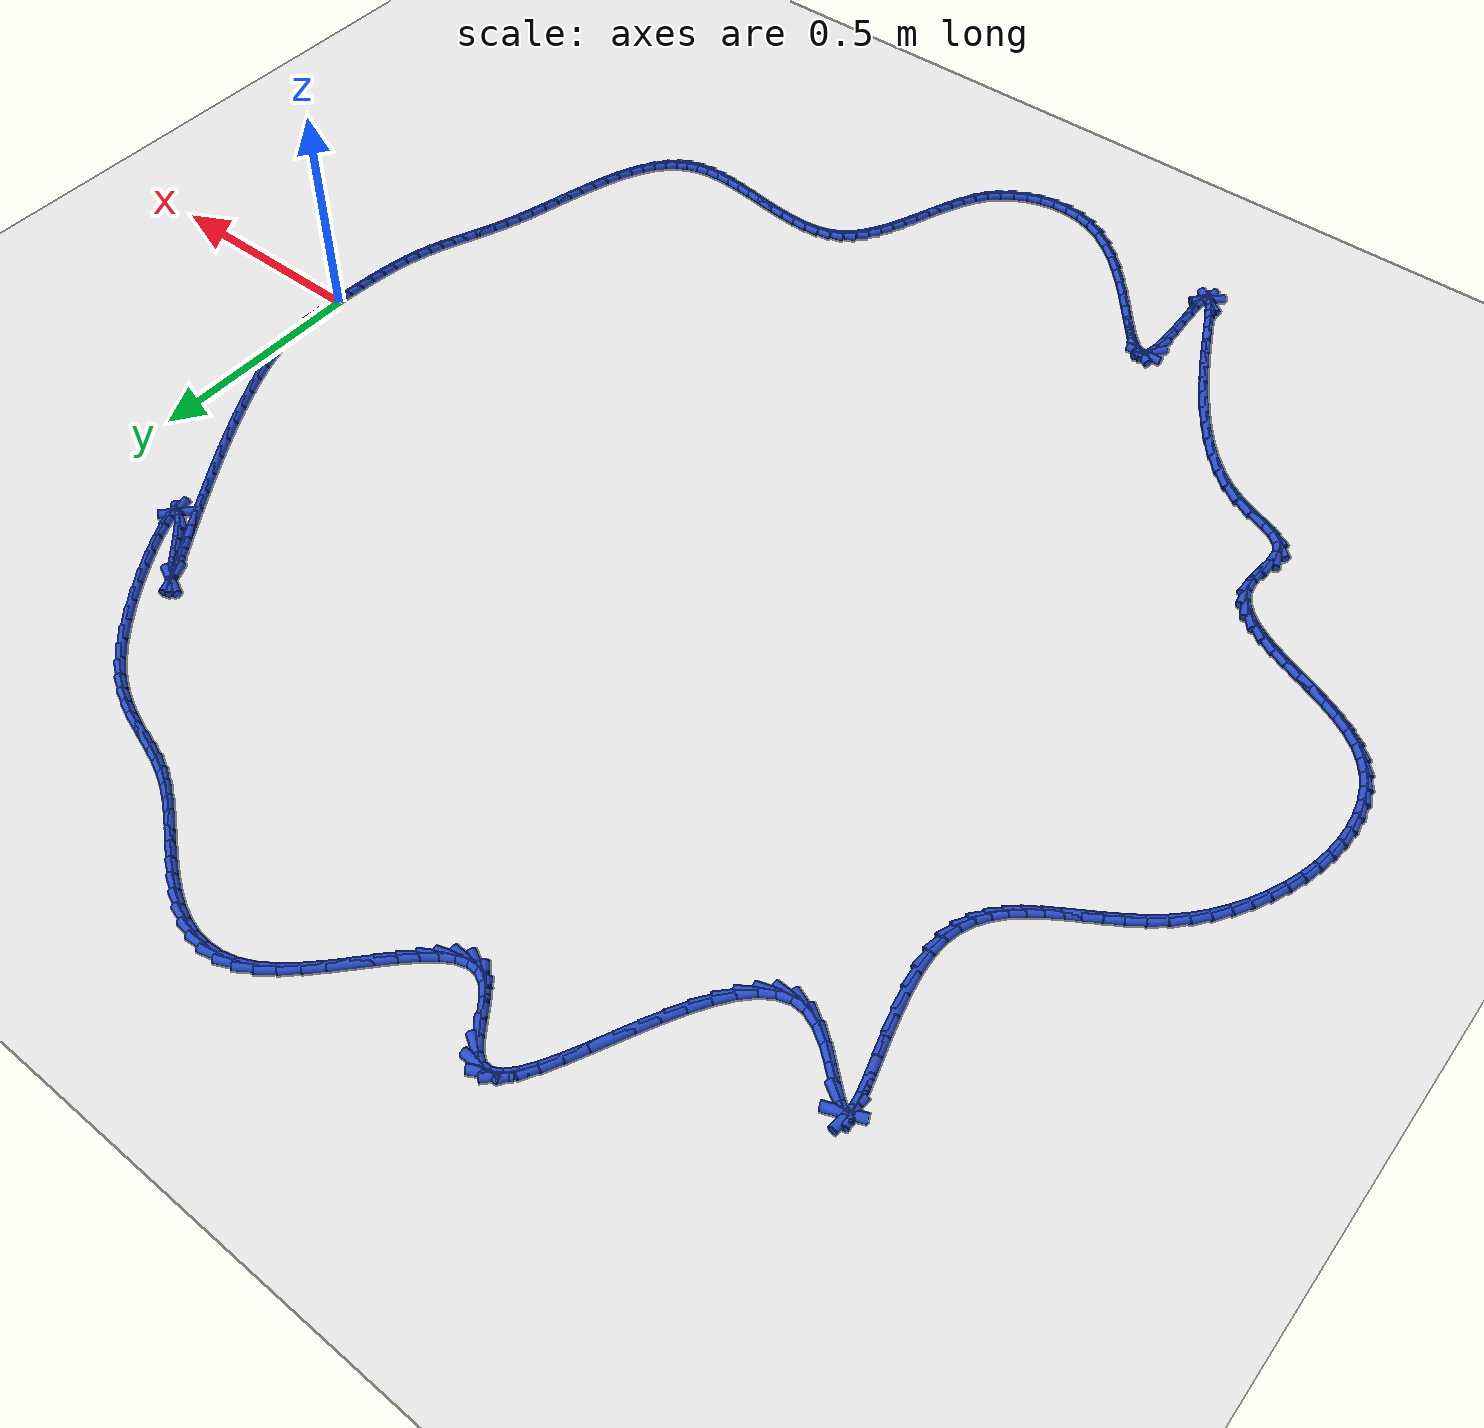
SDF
<sdf version="1.6">
 <world name="default">
  <light name="sun" type="directional">
   <pose>0 0 10 0 -0 0</pose>
   <diffuse>0.8 0.8 0.8 1</diffuse>
   <specular>0.2 0.2 0.2 1</specular>
   <attenuation>
    <range>1000</range>
    <constant>0.9</constant>
    <linear>0.01</linear>
    <quadratic>0.001</quadratic>
   </attenuation>
   <direction>-0.5 0.1 -0.9</direction>
  </light>
  <model name="ground_plane">
   <static>1</static>
   <link name="link">
    <collision name="collision">
     <geometry><plane><normal>0 0 1</normal><size>100 100</size></plane></geometry>
     <surface><friction><ode><mu>100</mu><mu2>50</mu2></ode></friction></surface>
    </collision>
    <visual name="visual">
     <cast_shadows>0</cast_shadows>
     <geometry><plane><normal>0 0 1</normal><size>100 100</size></plane></geometry>
     <material>
      <script><uri>file://media/materials/scripts/gazebo.material</uri><name>Gazebo/WhiteGlow</name></script>
     </material>
    </visual>
   </link>
  </model>
  <gravity>0 0 -9.8</gravity>
  <magnetic_field>6e-06 2.3e-05 -4.2e-05</magnetic_field>
  <atmosphere type="adiabatic"/>
  <physics name="default_physics" default="0" type="ode">
   <max_step_size>0.001</max_step_size>
   <real_time_factor>1</real_time_factor>
   <real_time_update_rate>1000</real_time_update_rate>
  </physics>
  <scene><ambient>0.4 0.4 0.4 1</ambient><background>0.7 0.7 0.7 1</background><shadows>1</shadows></scene>
  <spherical_coordinates>
   <surface_model>EARTH_WGS84</surface_model>
   <latitude_deg>0</latitude_deg>
   <longitude_deg>0</longitude_deg>
   <elevation>0</elevation>
   <heading_deg>0</heading_deg>
  </spherical_coordinates>
  <model name="line">
   <link name="link_0">
    <pose>-1.452830911130576e-17 -1.3877787807814457e-17 0.01 0 1.57 1.5314146172962937</pose>
    <collision name="collision">
     <geometry><cylinder><radius>0.01</radius><length>0.08</length></cylinder></geometry>
    </collision>
    <visual name="visual">
     <material>
      <script><name>Gazebo/Blue</name><uri>file://media/materials/scripts/gazebo.material</uri></script>
     </material>
     <geometry><cylinder><radius>0.01</radius><length>0.08</length></cylinder></geometry>
    </visual>
   </link>
   <link name="link_1">
    <pose>0.0011957025855414834 0.03034617823514206 0.01 0 1.57 1.5527518922761108</pose>
    <collision name="collision">
     <geometry><cylinder><radius>0.01</radius><length>0.08</length></cylinder></geometry>
    </collision>
    <visual name="visual">
     <material>
      <script><name>Gazebo/Blue</name><uri>file://media/materials/scripts/gazebo.material</uri></script>
     </material>
     <geometry><cylinder><radius>0.01</radius><length>0.08</length></cylinder></geometry>
    </visual>
   </link>
   <link name="link_2">
    <pose>0.0017354182623642966 0.06025329987738771 0.01 0 1.57 -1.549297469735532</pose>
    <collision name="collision">
     <geometry><cylinder><radius>0.01</radius><length>0.08</length></cylinder></geometry>
    </collision>
    <visual name="visual">
     <material>
      <script><name>Gazebo/Blue</name><uri>file://media/materials/scripts/gazebo.material</uri></script>
     </material>
     <geometry><cylinder><radius>0.01</radius><length>0.08</length></cylinder></geometry>
    </visual>
   </link>
   <link name="link_3">
    <pose>0.001090332900022824 0.09025424230714581 0.01 0 1.57 -1.4939358844110877</pose>
    <collision name="collision">
     <geometry><cylinder><radius>0.01</radius><length>0.08</length></cylinder></geometry>
    </collision>
    <visual name="visual">
     <material>
      <script><name>Gazebo/Blue</name><uri>file://media/materials/scripts/gazebo.material</uri></script>
     </material>
     <geometry><cylinder><radius>0.01</radius><length>0.08</length></cylinder></geometry>
    </visual>
   </link>
   <link name="link_4">
    <pose>-0.0012683676319285384 0.12088188290482527 0.01 0 1.57 -1.4270469136256383</pose>
    <collision name="collision">
     <geometry><cylinder><radius>0.01</radius><length>0.08</length></cylinder></geometry>
    </collision>
    <visual name="visual">
     <material>
      <script><name>Gazebo/Blue</name><uri>file://media/materials/scripts/gazebo.material</uri></script>
     </material>
     <geometry><cylinder><radius>0.01</radius><length>0.08</length></cylinder></geometry>
    </visual>
   </link>
   <link name="link_5">
    <pose>-0.0058694974639353845 0.15266909905083492 0.01 0 1.57 -1.3540509860456753</pose>
    <collision name="collision">
     <geometry><cylinder><radius>0.01</radius><length>0.08</length></cylinder></geometry>
    </collision>
    <visual name="visual">
     <material>
      <script><name>Gazebo/Blue</name><uri>file://media/materials/scripts/gazebo.material</uri></script>
     </material>
     <geometry><cylinder><radius>0.01</radius><length>0.08</length></cylinder></geometry>
    </visual>
   </link>
   <link name="link_6">
    <pose>-0.013241870726443332 0.18614876812558376 0.01 0 1.57 -1.2803437025456075</pose>
    <collision name="collision">
     <geometry><cylinder><radius>0.01</radius><length>0.08</length></cylinder></geometry>
    </collision>
    <visual name="visual">
     <material>
      <script><name>Gazebo/Blue</name><uri>file://media/materials/scripts/gazebo.material</uri></script>
     </material>
     <geometry><cylinder><radius>0.01</radius><length>0.08</length></cylinder></geometry>
    </visual>
   </link>
   <link name="link_7">
    <pose>-0.023914301549897977 0.22185376750948052 0.01 0 1.57 -1.2114050068358515</pose>
    <collision name="collision">
     <geometry><cylinder><radius>0.01</radius><length>0.08</length></cylinder></geometry>
    </collision>
    <visual name="visual">
     <material>
      <script><name>Gazebo/Blue</name><uri>file://media/materials/scripts/gazebo.material</uri></script>
     </material>
     <geometry><cylinder><radius>0.01</radius><length>0.08</length></cylinder></geometry>
    </visual>
   </link>
   <link name="link_8">
    <pose>-0.03833355045311387 0.2602326290638309 0.01 0 1.57 -1.1566921765645992</pose>
    <collision name="collision">
     <geometry><cylinder><radius>0.01</radius><length>0.08</length></cylinder></geometry>
    </collision>
    <visual name="visual">
     <material>
      <script><name>Gazebo/Blue</name><uri>file://media/materials/scripts/gazebo.material</uri></script>
     </material>
     <geometry><cylinder><radius>0.01</radius><length>0.08</length></cylinder></geometry>
    </visual>
   </link>
   <link name="link_9">
    <pose>-0.05626739566768492 0.3010359371453852 0.01 0 1.57 -1.1153612259383174</pose>
    <collision name="collision">
     <geometry><cylinder><radius>0.01</radius><length>0.08</length></cylinder></geometry>
    </collision>
    <visual name="visual">
     <material>
      <script><name>Gazebo/Blue</name><uri>file://media/materials/scripts/gazebo.material</uri></script>
     </material>
     <geometry><cylinder><radius>0.01</radius><length>0.08</length></cylinder></geometry>
    </visual>
   </link>
   <link name="link_10">
    <pose>-0.07714838643177577 0.34366968355844885 0.01 0 1.57 -1.0832880244415644</pose>
    <collision name="collision">
     <geometry><cylinder><radius>0.01</radius><length>0.08</length></cylinder></geometry>
    </collision>
    <visual name="visual">
     <material>
      <script><name>Gazebo/Blue</name><uri>file://media/materials/scripts/gazebo.material</uri></script>
     </material>
     <geometry><cylinder><radius>0.01</radius><length>0.08</length></cylinder></geometry>
    </visual>
   </link>
   <link name="link_11">
    <pose>-0.1004067029873917 0.3875374249407714 0.01 0 1.57 -1.0578677422182863</pose>
    <collision name="collision">
     <geometry><cylinder><radius>0.01</radius><length>0.08</length></cylinder></geometry>
    </collision>
    <visual name="visual">
     <material>
      <script><name>Gazebo/Blue</name><uri>file://media/materials/scripts/gazebo.material</uri></script>
     </material>
     <geometry><cylinder><radius>0.01</radius><length>0.08</length></cylinder></geometry>
    </visual>
   </link>
   <link name="link_12">
    <pose>-0.12547252557653785 0.4320427179301024 0.01 0 1.57 -1.037410398256839</pose>
    <collision name="collision">
     <geometry><cylinder><radius>0.01</radius><length>0.08</length></cylinder></geometry>
    </collision>
    <visual name="visual">
     <material>
      <script><name>Gazebo/Blue</name><uri>file://media/materials/scripts/gazebo.material</uri></script>
     </material>
     <geometry><cylinder><radius>0.01</radius><length>0.08</length></cylinder></geometry>
    </visual>
   </link>
   <link name="link_13">
    <pose>-0.15177603444121956 0.4765891191641915 0.01 0 1.57 -1.0207926357691341</pose>
    <collision name="collision">
     <geometry><cylinder><radius>0.01</radius><length>0.08</length></cylinder></geometry>
    </collision>
    <visual name="visual">
     <material>
      <script><name>Gazebo/Blue</name><uri>file://media/materials/scripts/gazebo.material</uri></script>
     </material>
     <geometry><cylinder><radius>0.01</radius><length>0.08</length></cylinder></geometry>
    </visual>
   </link>
   <link name="link_14">
    <pose>-0.17874740982344212 0.5205801852807884 0.01 0 1.57 -1.0072626667277371</pose>
    <collision name="collision">
     <geometry><cylinder><radius>0.01</radius><length>0.08</length></cylinder></geometry>
    </collision>
    <visual name="visual">
     <material>
      <script><name>Gazebo/Blue</name><uri>file://media/materials/scripts/gazebo.material</uri></script>
     </material>
     <geometry><cylinder><radius>0.01</radius><length>0.08</length></cylinder></geometry>
    </visual>
   </link>
   <link name="link_15">
    <pose>-0.20581683196521067 0.5634194729176425 0.01 0 1.57 -0.9963317668894072</pose>
    <collision name="collision">
     <geometry><cylinder><radius>0.01</radius><length>0.08</length></cylinder></geometry>
    </collision>
    <visual name="visual">
     <material>
      <script><name>Gazebo/Blue</name><uri>file://media/materials/scripts/gazebo.material</uri></script>
     </material>
     <geometry><cylinder><radius>0.01</radius><length>0.08</length></cylinder></geometry>
    </visual>
   </link>
   <link name="link_16">
    <pose>-0.23241448110853055 0.6045105387125034 0.01 0 1.57 -0.9877212336688247</pose>
    <collision name="collision">
     <geometry><cylinder><radius>0.01</radius><length>0.08</length></cylinder></geometry>
    </collision>
    <visual name="visual">
     <material>
      <script><name>Gazebo/Blue</name><uri>file://media/materials/scripts/gazebo.material</uri></script>
     </material>
     <geometry><cylinder><radius>0.01</radius><length>0.08</length></cylinder></geometry>
    </visual>
   </link>
   <link name="link_17">
    <pose>-0.25797053749540705 0.643256939303121 0.01 0 1.57 -0.9813556035505789</pose>
    <collision name="collision">
     <geometry><cylinder><radius>0.01</radius><length>0.08</length></cylinder></geometry>
    </collision>
    <visual name="visual">
     <material>
      <script><name>Gazebo/Blue</name><uri>file://media/materials/scripts/gazebo.material</uri></script>
     </material>
     <geometry><cylinder><radius>0.01</radius><length>0.08</length></cylinder></geometry>
    </visual>
   </link>
   <link name="link_18">
    <pose>-0.2819151813678453 0.6790622313272446 0.01 0 1.57 -0.97741535014258</pose>
    <collision name="collision">
     <geometry><cylinder><radius>0.01</radius><length>0.08</length></cylinder></geometry>
    </collision>
    <visual name="visual">
     <material>
      <script><name>Gazebo/Blue</name><uri>file://media/materials/scripts/gazebo.material</uri></script>
     </material>
     <geometry><cylinder><radius>0.01</radius><length>0.08</length></cylinder></geometry>
    </visual>
   </link>
   <link name="link_19">
    <pose>-0.3036785929678507 0.7113299714226238 0.01 0 1.57 -0.9765076463094204</pose>
    <collision name="collision">
     <geometry><cylinder><radius>0.01</radius><length>0.08</length></cylinder></geometry>
    </collision>
    <visual name="visual">
     <material>
      <script><name>Gazebo/Blue</name><uri>file://media/materials/scripts/gazebo.material</uri></script>
     </material>
     <geometry><cylinder><radius>0.01</radius><length>0.08</length></cylinder></geometry>
    </visual>
   </link>
   <link name="link_20">
    <pose>-0.3226909525374284 0.7394637162270085 0.01 0 1.57 -0.9801572158109034</pose>
    <collision name="collision">
     <geometry><cylinder><radius>0.01</radius><length>0.08</length></cylinder></geometry>
    </collision>
    <visual name="visual">
     <material>
      <script><name>Gazebo/Blue</name><uri>file://media/materials/scripts/gazebo.material</uri></script>
     </material>
     <geometry><cylinder><radius>0.01</radius><length>0.08</length></cylinder></geometry>
    </visual>
   </link>
   <link name="link_21">
    <pose>-0.3383824403185837 0.762867022378148 0.01 0 1.57 -0.9924356090517462</pose>
    <collision name="collision">
     <geometry><cylinder><radius>0.01</radius><length>0.08</length></cylinder></geometry>
    </collision>
    <visual name="visual">
     <material>
      <script><name>Gazebo/Blue</name><uri>file://media/materials/scripts/gazebo.material</uri></script>
     </material>
     <geometry><cylinder><radius>0.01</radius><length>0.08</length></cylinder></geometry>
    </visual>
   </link>
   <link name="link_22">
    <pose>-0.3501832365533219 0.7809434465137919 0.01 0 1.57 -1.0274520968835432</pose>
    <collision name="collision">
     <geometry><cylinder><radius>0.01</radius><length>0.08</length></cylinder></geometry>
    </collision>
    <visual name="visual">
     <material>
      <script><name>Gazebo/Blue</name><uri>file://media/materials/scripts/gazebo.material</uri></script>
     </material>
     <geometry><cylinder><radius>0.01</radius><length>0.08</length></cylinder></geometry>
    </visual>
   </link>
   <link name="link_23">
    <pose>-0.3575235214836482 0.79309654527169 0.01 0 1.57 -1.1816552442879247</pose>
    <collision name="collision">
     <geometry><cylinder><radius>0.01</radius><length>0.08</length></cylinder></geometry>
    </collision>
    <visual name="visual">
     <material>
      <script><name>Gazebo/Blue</name><uri>file://media/materials/scripts/gazebo.material</uri></script>
     </material>
     <geometry><cylinder><radius>0.01</radius><length>0.08</length></cylinder></geometry>
    </visual>
   </link>
   <link name="link_24">
    <pose>-0.3598334753515678 0.7987298752895919 0.01 0 1.57 -0.4234334483090144</pose>
    <collision name="collision">
     <geometry><cylinder><radius>0.01</radius><length>0.08</length></cylinder></geometry>
    </collision>
    <visual name="visual">
     <material>
      <script><name>Gazebo/Blue</name><uri>file://media/materials/scripts/gazebo.material</uri></script>
     </material>
     <geometry><cylinder><radius>0.01</radius><length>0.08</length></cylinder></geometry>
    </visual>
   </link>
   <link name="link_25">
    <pose>-0.35654327839908617 0.7972469932052473 0.01 0 1.57 -0.7712141787073871</pose>
    <collision name="collision">
     <geometry><cylinder><radius>0.01</radius><length>0.08</length></cylinder></geometry>
    </collision>
    <visual name="visual">
     <material>
      <script><name>Gazebo/Blue</name><uri>file://media/materials/scripts/gazebo.material</uri></script>
     </material>
     <geometry><cylinder><radius>0.01</radius><length>0.08</length></cylinder></geometry>
    </visual>
   </link>
   <link name="link_26">
    <pose>-0.3470831108682083 0.7880514556564053 0.01 0 1.57 -0.8240149284664824</pose>
    <collision name="collision">
     <geometry><cylinder><radius>0.01</radius><length>0.08</length></cylinder></geometry>
    </collision>
    <visual name="visual">
     <material>
      <script><name>Gazebo/Blue</name><uri>file://media/materials/scripts/gazebo.material</uri></script>
     </material>
     <geometry><cylinder><radius>0.01</radius><length>0.08</length></cylinder></geometry>
    </visual>
   </link>
   <link name="link_27">
    <pose>-0.3308936259842423 0.7705607020082742 0.01 0 1.57 -0.8380627643055365</pose>
    <collision name="collision">
     <geometry><cylinder><radius>0.01</radius><length>0.08</length></cylinder></geometry>
    </collision>
    <visual name="visual">
     <material>
      <script><name>Gazebo/Blue</name><uri>file://media/materials/scripts/gazebo.material</uri></script>
     </material>
     <geometry><cylinder><radius>0.01</radius><length>0.08</length></cylinder></geometry>
    </visual>
   </link>
   <link name="link_28">
    <pose>-0.3087101262112666 0.7459083266142429 0.01 0 1.57 -0.8315883247613354</pose>
    <collision name="collision">
     <geometry><cylinder><radius>0.01</radius><length>0.08</length></cylinder></geometry>
    </collision>
    <visual name="visual">
     <material>
      <script><name>Gazebo/Blue</name><uri>file://media/materials/scripts/gazebo.material</uri></script>
     </material>
     <geometry><cylinder><radius>0.01</radius><length>0.08</length></cylinder></geometry>
    </visual>
   </link>
   <link name="link_29">
    <pose>-0.28379719895911654 0.7185806813516706 0.01 0 1.57 -0.8065985358899385</pose>
    <collision name="collision">
     <geometry><cylinder><radius>0.01</radius><length>0.08</length></cylinder></geometry>
    </collision>
    <visual name="visual">
     <material>
      <script><name>Gazebo/Blue</name><uri>file://media/materials/scripts/gazebo.material</uri></script>
     </material>
     <geometry><cylinder><radius>0.01</radius><length>0.08</length></cylinder></geometry>
    </visual>
   </link>
   <link name="link_30">
    <pose>-0.25971211834724517 0.6934520963561535 0.01 0 1.57 -0.7418616986053189</pose>
    <collision name="collision">
     <geometry><cylinder><radius>0.01</radius><length>0.08</length></cylinder></geometry>
    </collision>
    <visual name="visual">
     <material>
      <script><name>Gazebo/Blue</name><uri>file://media/materials/scripts/gazebo.material</uri></script>
     </material>
     <geometry><cylinder><radius>0.01</radius><length>0.08</length></cylinder></geometry>
    </visual>
   </link>
   <link name="link_31">
    <pose>-0.24001215849510626 0.6753969017632875 0.01 0 1.57 -0.5046648595675626</pose>
    <collision name="collision">
     <geometry><cylinder><radius>0.01</radius><length>0.08</length></cylinder></geometry>
    </collision>
    <visual name="visual">
     <material>
      <script><name>Gazebo/Blue</name><uri>file://media/materials/scripts/gazebo.material</uri></script>
     </material>
     <geometry><cylinder><radius>0.01</radius><length>0.08</length></cylinder></geometry>
    </visual>
   </link>
   <link name="link_32">
    <pose>-0.22784411909766647 0.6686755800326889 0.01 0 1.57 0.8357996603777357</pose>
    <collision name="collision">
     <geometry><cylinder><radius>0.01</radius><length>0.08</length></cylinder></geometry>
    </collision>
    <visual name="visual">
     <material>
      <script><name>Gazebo/Blue</name><uri>file://media/materials/scripts/gazebo.material</uri></script>
     </material>
     <geometry><cylinder><radius>0.01</radius><length>0.08</length></cylinder></geometry>
    </visual>
   </link>
   <link name="link_33">
    <pose>-0.22357759358885643 0.6733954155016149 0.01 0 1.57 -1.3770946573760192</pose>
    <collision name="collision">
     <geometry><cylinder><radius>0.01</radius><length>0.08</length></cylinder></geometry>
    </collision>
    <visual name="visual">
     <material>
      <script><name>Gazebo/Blue</name><uri>file://media/materials/scripts/gazebo.material</uri></script>
     </material>
     <geometry><cylinder><radius>0.01</radius><length>0.08</length></cylinder></geometry>
    </visual>
   </link>
   <link name="link_34">
    <pose>-0.22643114071247908 0.6879423673105319 0.01 0 1.57 -1.1870102844306587</pose>
    <collision name="collision">
     <geometry><cylinder><radius>0.01</radius><length>0.08</length></cylinder></geometry>
    </collision>
    <visual name="visual">
     <material>
      <script><name>Gazebo/Blue</name><uri>file://media/materials/scripts/gazebo.material</uri></script>
     </material>
     <geometry><cylinder><radius>0.01</radius><length>0.08</length></cylinder></geometry>
    </visual>
   </link>
   <link name="link_35">
    <pose>-0.23561962079070545 0.7106968637619583 0.01 0 1.57 -1.1053226309123712</pose>
    <collision name="collision">
     <geometry><cylinder><radius>0.01</radius><length>0.08</length></cylinder></geometry>
    </collision>
    <visual name="visual">
     <material>
      <script><name>Gazebo/Blue</name><uri>file://media/materials/scripts/gazebo.material</uri></script>
     </material>
     <geometry><cylinder><radius>0.01</radius><length>0.08</length></cylinder></geometry>
    </visual>
   </link>
   <link name="link_36">
    <pose>-0.25035789414570697 0.7400393331584132 0.01 0 1.57 -1.053922432441229</pose>
    <collision name="collision">
     <geometry><cylinder><radius>0.01</radius><length>0.08</length></cylinder></geometry>
    </collision>
    <visual name="visual">
     <material>
      <script><name>Gazebo/Blue</name><uri>file://media/materials/scripts/gazebo.material</uri></script>
     </material>
     <geometry><cylinder><radius>0.01</radius><length>0.08</length></cylinder></geometry>
    </visual>
   </link>
   <link name="link_37">
    <pose>-0.2698608210996544 0.7743502038024145 0.01 0 1.57 -1.013245457825605</pose>
    <collision name="collision">
     <geometry><cylinder><radius>0.01</radius><length>0.08</length></cylinder></geometry>
    </collision>
    <visual name="visual">
     <material>
      <script><name>Gazebo/Blue</name><uri>file://media/materials/scripts/gazebo.material</uri></script>
     </material>
     <geometry><cylinder><radius>0.01</radius><length>0.08</length></cylinder></geometry>
    </visual>
   </link>
   <link name="link_38">
    <pose>-0.2933432619747191 0.812009903996481 0.01 0 1.57 -0.9754913485099312</pose>
    <collision name="collision">
     <geometry><cylinder><radius>0.01</radius><length>0.08</length></cylinder></geometry>
    </collision>
    <visual name="visual">
     <material>
      <script><name>Gazebo/Blue</name><uri>file://media/materials/scripts/gazebo.material</uri></script>
     </material>
     <geometry><cylinder><radius>0.01</radius><length>0.08</length></cylinder></geometry>
    </visual>
   </link>
   <link name="link_39">
    <pose>-0.32002007709307195 0.8513988620431314 0.01 0 1.57 -0.9360685299195783</pose>
    <collision name="collision">
     <geometry><cylinder><radius>0.01</radius><length>0.08</length></cylinder></geometry>
    </collision>
    <visual name="visual">
     <material>
      <script><name>Gazebo/Blue</name><uri>file://media/materials/scripts/gazebo.material</uri></script>
     </material>
     <geometry><cylinder><radius>0.01</radius><length>0.08</length></cylinder></geometry>
    </visual>
   </link>
   <link name="link_40">
    <pose>-0.34910612677688396 0.8908975062448835 0.01 0 1.57 -0.8909538688888938</pose>
    <collision name="collision">
     <geometry><cylinder><radius>0.01</radius><length>0.08</length></cylinder></geometry>
    </collision>
    <visual name="visual">
     <material>
      <script><name>Gazebo/Blue</name><uri>file://media/materials/scripts/gazebo.material</uri></script>
     </material>
     <geometry><cylinder><radius>0.01</radius><length>0.08</length></cylinder></geometry>
    </visual>
   </link>
   <link name="link_41">
    <pose>-0.3798162713483267 0.9288862649042571 0.01 0 1.57 -0.835203069238861</pose>
    <collision name="collision">
     <geometry><cylinder><radius>0.01</radius><length>0.08</length></cylinder></geometry>
    </collision>
    <visual name="visual">
     <material>
      <script><name>Gazebo/Blue</name><uri>file://media/materials/scripts/gazebo.material</uri></script>
     </material>
     <geometry><cylinder><radius>0.01</radius><length>0.08</length></cylinder></geometry>
    </visual>
   </link>
   <link name="link_42">
    <pose>-0.41136537112957083 0.9637455663237696 0.01 0 1.57 -0.7612328210769039</pose>
    <collision name="collision">
     <geometry><cylinder><radius>0.01</radius><length>0.08</length></cylinder></geometry>
    </collision>
    <visual name="visual">
     <material>
      <script><name>Gazebo/Blue</name><uri>file://media/materials/scripts/gazebo.material</uri></script>
     </material>
     <geometry><cylinder><radius>0.01</radius><length>0.08</length></cylinder></geometry>
    </visual>
   </link>
   <link name="link_43">
    <pose>-0.44296873541837195 0.993857274393652 0.01 0 1.57 -0.6655791075287187</pose>
    <collision name="collision">
     <geometry><cylinder><radius>0.01</radius><length>0.08</length></cylinder></geometry>
    </collision>
    <visual name="visual">
     <material>
      <script><name>Gazebo/Blue</name><uri>file://media/materials/scripts/gazebo.material</uri></script>
     </material>
     <geometry><cylinder><radius>0.01</radius><length>0.08</length></cylinder></geometry>
    </visual>
   </link>
   <link name="link_44">
    <pose>-0.47404556082668414 1.0182551773696116 0.01 0 1.57 -0.5665526695248854</pose>
    <collision name="collision">
     <geometry><cylinder><radius>0.01</radius><length>0.08</length></cylinder></geometry>
    </collision>
    <visual name="visual">
     <material>
      <script><name>Gazebo/Blue</name><uri>file://media/materials/scripts/gazebo.material</uri></script>
     </material>
     <geometry><cylinder><radius>0.01</radius><length>0.08</length></cylinder></geometry>
    </visual>
   </link>
   <link name="link_45">
    <pose>-0.5045406128687585 1.0376535563545468 0.01 0 1.57 -0.47452770525399474</pose>
    <collision name="collision">
     <geometry><cylinder><radius>0.01</radius><length>0.08</length></cylinder></geometry>
    </collision>
    <visual name="visual">
     <material>
      <script><name>Gazebo/Blue</name><uri>file://media/materials/scripts/gazebo.material</uri></script>
     </material>
     <geometry><cylinder><radius>0.01</radius><length>0.08</length></cylinder></geometry>
    </visual>
   </link>
   <link name="link_46">
    <pose>-0.534482193994335 1.0530337996221815 0.01 0 1.57 -0.39729859071451834</pose>
    <collision name="collision">
     <geometry><cylinder><radius>0.01</radius><length>0.08</length></cylinder></geometry>
    </collision>
    <visual name="visual">
     <material>
      <script><name>Gazebo/Blue</name><uri>file://media/materials/scripts/gazebo.material</uri></script>
     </material>
     <geometry><cylinder><radius>0.01</radius><length>0.08</length></cylinder></geometry>
    </visual>
   </link>
   <link name="link_47">
    <pose>-0.5638986066531552 1.0653772954462397 0.01 0 1.57 -0.34178834530915303</pose>
    <collision name="collision">
     <geometry><cylinder><radius>0.01</radius><length>0.08</length></cylinder></geometry>
    </collision>
    <visual name="visual">
     <material>
      <script><name>Gazebo/Blue</name><uri>file://media/materials/scripts/gazebo.material</uri></script>
     </material>
     <geometry><cylinder><radius>0.01</radius><length>0.08</length></cylinder></geometry>
    </visual>
   </link>
   <link name="link_48">
    <pose>-0.5928181532949586 1.0756654321004455 0.01 0 1.57 -0.3132014292212567</pose>
    <collision name="collision">
     <geometry><cylinder><radius>0.01</radius><length>0.08</length></cylinder></geometry>
    </collision>
    <visual name="visual">
     <material>
      <script><name>Gazebo/Blue</name><uri>file://media/materials/scripts/gazebo.material</uri></script>
     </material>
     <geometry><cylinder><radius>0.01</radius><length>0.08</length></cylinder></geometry>
    </visual>
   </link>
   <link name="link_49">
    <pose>-0.6212691363694862 1.0848795978585228 0.01 0 1.57 -0.31481618833116337</pose>
    <collision name="collision">
     <geometry><cylinder><radius>0.01</radius><length>0.08</length></cylinder></geometry>
    </collision>
    <visual name="visual">
     <material>
      <script><name>Gazebo/Blue</name><uri>file://media/materials/scripts/gazebo.material</uri></script>
     </material>
     <geometry><cylinder><radius>0.01</radius><length>0.08</length></cylinder></geometry>
    </visual>
   </link>
   <link name="link_50">
    <pose>-0.6492798583264782 1.0940011809941956 0.01 0 1.57 -0.3479539092925341</pose>
    <collision name="collision">
     <geometry><cylinder><radius>0.01</radius><length>0.08</length></cylinder></geometry>
    </collision>
    <visual name="visual">
     <material>
      <script><name>Gazebo/Blue</name><uri>file://media/materials/scripts/gazebo.material</uri></script>
     </material>
     <geometry><cylinder><radius>0.01</radius><length>0.08</length></cylinder></geometry>
    </visual>
   </link>
   <link name="link_51">
    <pose>-0.6768786216156751 1.1040115697811879 0.01 0 1.57 -0.4116074694319122</pose>
    <collision name="collision">
     <geometry><cylinder><radius>0.01</radius><length>0.08</length></cylinder></geometry>
    </collision>
    <visual name="visual">
     <material>
      <script><name>Gazebo/Blue</name><uri>file://media/materials/scripts/gazebo.material</uri></script>
     </material>
     <geometry><cylinder><radius>0.01</radius><length>0.08</length></cylinder></geometry>
    </visual>
   </link>
   <link name="link_52">
    <pose>-0.7040937286868176 1.1158921524932235 0.01 0 1.57 -0.499039388053943</pose>
    <collision name="collision">
     <geometry><cylinder><radius>0.01</radius><length>0.08</length></cylinder></geometry>
    </collision>
    <visual name="visual">
     <material>
      <script><name>Gazebo/Blue</name><uri>file://media/materials/scripts/gazebo.material</uri></script>
     </material>
     <geometry><cylinder><radius>0.01</radius><length>0.08</length></cylinder></geometry>
    </visual>
   </link>
   <link name="link_53">
    <pose>-0.7309586160008682 1.130535016229455 0.01 0 1.57 -0.5765115334328594</pose>
    <collision name="collision">
     <geometry><cylinder><radius>0.01</radius><length>0.08</length></cylinder></geometry>
    </collision>
    <visual name="visual">
     <material>
      <script><name>Gazebo/Blue</name><uri>file://media/materials/scripts/gazebo.material</uri></script>
     </material>
     <geometry><cylinder><radius>0.01</radius><length>0.08</length></cylinder></geometry>
    </visual>
   </link>
   <link name="link_54">
    <pose>-0.757564124297152 1.1478337560207574 0.01 0 1.57 -0.6280373991442904</pose>
    <collision name="collision">
     <geometry><cylinder><radius>0.01</radius><length>0.08</length></cylinder></geometry>
    </collision>
    <visual name="visual">
     <material>
      <script><name>Gazebo/Blue</name><uri>file://media/materials/scripts/gazebo.material</uri></script>
     </material>
     <geometry><cylinder><radius>0.01</radius><length>0.08</length></cylinder></geometry>
    </visual>
   </link>
   <link name="link_55">
    <pose>-0.7840370753121501 1.1670561121482994 0.01 0 1.57 -0.6567451833138885</pose>
    <collision name="collision">
     <geometry><cylinder><radius>0.01</radius><length>0.08</length></cylinder></geometry>
    </collision>
    <visual name="visual">
     <material>
      <script><name>Gazebo/Blue</name><uri>file://media/materials/scripts/gazebo.material</uri></script>
     </material>
     <geometry><cylinder><radius>0.01</radius><length>0.08</length></cylinder></geometry>
    </visual>
   </link>
   <link name="link_56">
    <pose>-0.8105048448410335 1.1874601875765962 0.01 0 1.57 -0.6648470650109151</pose>
    <collision name="collision">
     <geometry><cylinder><radius>0.01</radius><length>0.08</length></cylinder></geometry>
    </collision>
    <visual name="visual">
     <material>
      <script><name>Gazebo/Blue</name><uri>file://media/materials/scripts/gazebo.material</uri></script>
     </material>
     <geometry><cylinder><radius>0.01</radius><length>0.08</length></cylinder></geometry>
    </visual>
   </link>
   <link name="link_57">
    <pose>-0.8370948086789722 1.2083040852701608 0.01 0 1.57 -0.6532573071046962</pose>
    <collision name="collision">
     <geometry><cylinder><radius>0.01</radius><length>0.08</length></cylinder></geometry>
    </collision>
    <visual name="visual">
     <material>
      <script><name>Gazebo/Blue</name><uri>file://media/materials/scripts/gazebo.material</uri></script>
     </material>
     <geometry><cylinder><radius>0.01</radius><length>0.08</length></cylinder></geometry>
    </visual>
   </link>
   <link name="link_58">
    <pose>-0.8639343426211386 1.228845908193509 0.01 0 1.57 -0.6216472356482553</pose>
    <collision name="collision">
     <geometry><cylinder><radius>0.01</radius><length>0.08</length></cylinder></geometry>
    </collision>
    <visual name="visual">
     <material>
      <script><name>Gazebo/Blue</name><uri>file://media/materials/scripts/gazebo.material</uri></script>
     </material>
     <geometry><cylinder><radius>0.01</radius><length>0.08</length></cylinder></geometry>
    </visual>
   </link>
   <link name="link_59">
    <pose>-0.891150822462703 1.248343759311154 0.01 0 1.57 -0.5685622092272419</pose>
    <collision name="collision">
     <geometry><cylinder><radius>0.01</radius><length>0.08</length></cylinder></geometry>
    </collision>
    <visual name="visual">
     <material>
      <script><name>Gazebo/Blue</name><uri>file://media/materials/scripts/gazebo.material</uri></script>
     </material>
     <geometry><cylinder><radius>0.01</radius><length>0.08</length></cylinder></geometry>
    </visual>
   </link>
   <link name="link_60">
    <pose>-0.9188716239988364 1.2660557415876106 0.01 0 1.57 -0.49168249041199735</pose>
    <collision name="collision">
     <geometry><cylinder><radius>0.01</radius><length>0.08</length></cylinder></geometry>
    </collision>
    <visual name="visual">
     <material>
      <script><name>Gazebo/Blue</name><uri>file://media/materials/scripts/gazebo.material</uri></script>
     </material>
     <geometry><cylinder><radius>0.01</radius><length>0.08</length></cylinder></geometry>
    </visual>
   </link>
   <link name="link_61">
    <pose>-0.9472241230247095 1.2812399579873932 0.01 0 1.57 -0.3884738982829614</pose>
    <collision name="collision">
     <geometry><cylinder><radius>0.01</radius><length>0.08</length></cylinder></geometry>
    </collision>
    <visual name="visual">
     <material>
      <script><name>Gazebo/Blue</name><uri>file://media/materials/scripts/gazebo.material</uri></script>
     </material>
     <geometry><cylinder><radius>0.01</radius><length>0.08</length></cylinder></geometry>
    </visual>
   </link>
   <link name="link_62">
    <pose>-0.9763356953354941 1.2931545114750163 0.01 0 1.57 -0.25759734334213913</pose>
    <collision name="collision">
     <geometry><cylinder><radius>0.01</radius><length>0.08</length></cylinder></geometry>
    </collision>
    <visual name="visual">
     <material>
      <script><name>Gazebo/Blue</name><uri>file://media/materials/scripts/gazebo.material</uri></script>
     </material>
     <geometry><cylinder><radius>0.01</radius><length>0.08</length></cylinder></geometry>
    </visual>
   </link>
   <link name="link_63">
    <pose>-1.0063337167263604 1.3010575050149935 0.01 0 1.57 -0.10126697652020848</pose>
    <collision name="collision">
     <geometry><cylinder><radius>0.01</radius><length>0.08</length></cylinder></geometry>
    </collision>
    <visual name="visual">
     <material>
      <script><name>Gazebo/Blue</name><uri>file://media/materials/scripts/gazebo.material</uri></script>
     </material>
     <geometry><cylinder><radius>0.01</radius><length>0.08</length></cylinder></geometry>
    </visual>
   </link>
   <link name="link_64">
    <pose>-1.0373355784310672 1.3042077457591437 0.01 0 1.57 0.07285795637370492</pose>
    <collision name="collision">
     <geometry><cylinder><radius>0.01</radius><length>0.08</length></cylinder></geometry>
    </collision>
    <visual name="visual">
     <material>
      <script><name>Gazebo/Blue</name><uri>file://media/materials/scripts/gazebo.material</uri></script>
     </material>
     <geometry><cylinder><radius>0.01</radius><length>0.08</length></cylinder></geometry>
    </visual>
   </link>
   <link name="link_65">
    <pose>-1.069105739952479 1.301888932292535 0.01 0 1.57 0.2599042513969622</pose>
    <collision name="collision">
     <geometry><cylinder><radius>0.01</radius><length>0.08</length></cylinder></geometry>
    </collision>
    <visual name="visual">
     <material>
      <script><name>Gazebo/Blue</name><uri>file://media/materials/scripts/gazebo.material</uri></script>
     </material>
     <geometry><cylinder><radius>0.01</radius><length>0.08</length></cylinder></geometry>
    </visual>
   </link>
   <link name="link_66">
    <pose>-1.1009695833628423 1.2934157302842366 0.01 0 1.57 0.4505139508296998</pose>
    <collision name="collision">
     <geometry><cylinder><radius>0.01</radius><length>0.08</length></cylinder></geometry>
    </collision>
    <visual name="visual">
     <material>
      <script><name>Gazebo/Blue</name><uri>file://media/materials/scripts/gazebo.material</uri></script>
     </material>
     <geometry><cylinder><radius>0.01</radius><length>0.08</length></cylinder></geometry>
    </visual>
   </link>
   <link name="link_67">
    <pose>-1.1322794664993863 1.278271481078573 0.01 0 1.57 0.6022304035378606</pose>
    <collision name="collision">
     <geometry><cylinder><radius>0.01</radius><length>0.08</length></cylinder></geometry>
    </collision>
    <visual name="visual">
     <material>
      <script><name>Gazebo/Blue</name><uri>file://media/materials/scripts/gazebo.material</uri></script>
     </material>
     <geometry><cylinder><radius>0.01</radius><length>0.08</length></cylinder></geometry>
    </visual>
   </link>
   <link name="link_68">
    <pose>-1.1628237823363055 1.2572748251911945 0.01 0 1.57 0.7060330936975208</pose>
    <collision name="collision">
     <geometry><cylinder><radius>0.01</radius><length>0.08</length></cylinder></geometry>
    </collision>
    <visual name="visual">
     <material>
      <script><name>Gazebo/Blue</name><uri>file://media/materials/scripts/gazebo.material</uri></script>
     </material>
     <geometry><cylinder><radius>0.01</radius><length>0.08</length></cylinder></geometry>
    </visual>
   </link>
   <link name="link_69">
    <pose>-1.1926003396604754 1.2318857109990473 0.01 0 1.57 0.7733556615438558</pose>
    <collision name="collision">
     <geometry><cylinder><radius>0.01</radius><length>0.08</length></cylinder></geometry>
    </collision>
    <visual name="visual">
     <material>
      <script><name>Gazebo/Blue</name><uri>file://media/materials/scripts/gazebo.material</uri></script>
     </material>
     <geometry><cylinder><radius>0.01</radius><length>0.08</length></cylinder></geometry>
    </visual>
   </link>
   <link name="link_70">
    <pose>-1.2216082746293986 1.2035681517737284 0.01 0 1.57 0.8119953114622698</pose>
    <collision name="collision">
     <geometry><cylinder><radius>0.01</radius><length>0.08</length></cylinder></geometry>
    </collision>
    <visual name="visual">
     <material>
      <script><name>Gazebo/Blue</name><uri>file://media/materials/scripts/gazebo.material</uri></script>
     </material>
     <geometry><cylinder><radius>0.01</radius><length>0.08</length></cylinder></geometry>
    </visual>
   </link>
   <link name="link_71">
    <pose>-1.2498467234005772 1.1737861607868347 0.01 0 1.57 0.8258004485538232</pose>
    <collision name="collision">
     <geometry><cylinder><radius>0.01</radius><length>0.08</length></cylinder></geometry>
    </collision>
    <visual name="visual">
     <material>
      <script><name>Gazebo/Blue</name><uri>file://media/materials/scripts/gazebo.material</uri></script>
     </material>
     <geometry><cylinder><radius>0.01</radius><length>0.08</length></cylinder></geometry>
    </visual>
   </link>
   <link name="link_72">
    <pose>-1.2773148221315134 1.1440037513099643 0.01 0 1.57 0.8148708450045724</pose>
    <collision name="collision">
     <geometry><cylinder><radius>0.01</radius><length>0.08</length></cylinder></geometry>
    </collision>
    <visual name="visual">
     <material>
      <script><name>Gazebo/Blue</name><uri>file://media/materials/scripts/gazebo.material</uri></script>
     </material>
     <geometry><cylinder><radius>0.01</radius><length>0.08</length></cylinder></geometry>
    </visual>
   </link>
   <link name="link_73">
    <pose>-1.3040117069797093 1.1156849366147144 0.01 0 1.57 0.775000215249241</pose>
    <collision name="collision">
     <geometry><cylinder><radius>0.01</radius><length>0.08</length></cylinder></geometry>
    </collision>
    <visual name="visual">
     <material>
      <script><name>Gazebo/Blue</name><uri>file://media/materials/scripts/gazebo.material</uri></script>
     </material>
     <geometry><cylinder><radius>0.01</radius><length>0.08</length></cylinder></geometry>
    </visual>
   </link>
   <link name="link_74">
    <pose>-1.3299365141026664 1.0902937299726825 0.01 0 1.57 0.6956690130868082</pose>
    <collision name="collision">
     <geometry><cylinder><radius>0.01</radius><length>0.08</length></cylinder></geometry>
    </collision>
    <visual name="visual">
     <material>
      <script><name>Gazebo/Blue</name><uri>file://media/materials/scripts/gazebo.material</uri></script>
     </material>
     <geometry><cylinder><radius>0.01</radius><length>0.08</length></cylinder></geometry>
    </visual>
   </link>
   <link name="link_75">
    <pose>-1.355088379657887 1.0692941446554656 0.01 0 1.57 0.5558709354532964</pose>
    <collision name="collision">
     <geometry><cylinder><radius>0.01</radius><length>0.08</length></cylinder></geometry>
    </collision>
    <visual name="visual">
     <material>
      <script><name>Gazebo/Blue</name><uri>file://media/materials/scripts/gazebo.material</uri></script>
     </material>
     <geometry><cylinder><radius>0.01</radius><length>0.08</length></cylinder></geometry>
    </visual>
   </link>
   <link name="link_76">
    <pose>-1.379466439802873 1.0541501939346616 0.01 0 1.57 0.32009120316125955</pose>
    <collision name="collision">
     <geometry><cylinder><radius>0.01</radius><length>0.08</length></cylinder></geometry>
    </collision>
    <visual name="visual">
     <material>
      <script><name>Gazebo/Blue</name><uri>file://media/materials/scripts/gazebo.material</uri></script>
     </material>
     <geometry><cylinder><radius>0.01</radius><length>0.08</length></cylinder></geometry>
    </visual>
   </link>
   <link name="link_77">
    <pose>-1.4030698306951268 1.0463258910818678 0.01 0 1.57 -0.042001054062786265</pose>
    <collision name="collision">
     <geometry><cylinder><radius>0.01</radius><length>0.08</length></cylinder></geometry>
    </collision>
    <visual name="visual">
     <material>
      <script><name>Gazebo/Blue</name><uri>file://media/materials/scripts/gazebo.material</uri></script>
     </material>
     <geometry><cylinder><radius>0.01</radius><length>0.08</length></cylinder></geometry>
    </visual>
   </link>
   <link name="link_78">
    <pose>-1.4258976884921502 1.0472852493686817 0.01 0 1.57 -0.4702033790401221</pose>
    <collision name="collision">
     <geometry><cylinder><radius>0.01</radius><length>0.08</length></cylinder></geometry>
    </collision>
    <visual name="visual">
     <material>
      <script><name>Gazebo/Blue</name><uri>file://media/materials/scripts/gazebo.material</uri></script>
     </material>
     <geometry><cylinder><radius>0.01</radius><length>0.08</length></cylinder></geometry>
    </visual>
   </link>
   <link name="link_79">
    <pose>-1.4479491493514451 1.0584922820667004 0.01 0 1.57 -0.7998623264071261</pose>
    <collision name="collision">
     <geometry><cylinder><radius>0.01</radius><length>0.08</length></cylinder></geometry>
    </collision>
    <visual name="visual">
     <material>
      <script><name>Gazebo/Blue</name><uri>file://media/materials/scripts/gazebo.material</uri></script>
     </material>
     <geometry><cylinder><radius>0.01</radius><length>0.08</length></cylinder></geometry>
    </visual>
   </link>
   <link name="link_80">
    <pose>-1.4692330966651799 1.0804010189776572 0.01 0 1.57 -0.9395240260426623</pose>
    <collision name="collision">
     <geometry><cylinder><radius>0.01</radius><length>0.08</length></cylinder></geometry>
    </collision>
    <visual name="visual">
     <material>
      <script><name>Gazebo/Blue</name><uri>file://media/materials/scripts/gazebo.material</uri></script>
     </material>
     <geometry><cylinder><radius>0.01</radius><length>0.08</length></cylinder></geometry>
    </visual>
   </link>
   <link name="link_81">
    <pose>-1.4898059306293878 1.1085419204927653 0.01 0 1.57 -0.9589189700152593</pose>
    <collision name="collision">
     <geometry><cylinder><radius>0.01</radius><length>0.08</length></cylinder></geometry>
    </collision>
    <visual name="visual">
     <material>
      <script><name>Gazebo/Blue</name><uri>file://media/materials/scripts/gazebo.material</uri></script>
     </material>
     <geometry><cylinder><radius>0.01</radius><length>0.08</length></cylinder></geometry>
    </visual>
   </link>
   <link name="link_82">
    <pose>-1.5097385093054665 1.136947360055595 0.01 0 1.57 -0.8646044907235039</pose>
    <collision name="collision">
     <geometry><cylinder><radius>0.01</radius><length>0.08</length></cylinder></geometry>
    </collision>
    <visual name="visual">
     <material>
      <script><name>Gazebo/Blue</name><uri>file://media/materials/scripts/gazebo.material</uri></script>
     </material>
     <geometry><cylinder><radius>0.01</radius><length>0.08</length></cylinder></geometry>
    </visual>
   </link>
   <link name="link_83">
    <pose>-1.5291016941559281 1.159649358695039 0.01 0 1.57 -0.5514637937763708</pose>
    <collision name="collision">
     <geometry><cylinder><radius>0.01</radius><length>0.08</length></cylinder></geometry>
    </collision>
    <visual name="visual">
     <material>
      <script><name>Gazebo/Blue</name><uri>file://media/materials/scripts/gazebo.material</uri></script>
     </material>
     <geometry><cylinder><radius>0.01</radius><length>0.08</length></cylinder></geometry>
    </visual>
   </link>
   <link name="link_84">
    <pose>-1.547971442976684 1.1712565384934222 0.01 0 1.57 0.013093412863579615</pose>
    <collision name="collision">
     <geometry><cylinder><radius>0.01</radius><length>0.08</length></cylinder></geometry>
    </collision>
    <visual name="visual">
     <material>
      <script><name>Gazebo/Blue</name><uri>file://media/materials/scripts/gazebo.material</uri></script>
     </material>
     <geometry><cylinder><radius>0.01</radius><length>0.08</length></cylinder></geometry>
    </visual>
   </link>
   <link name="link_85">
    <pose>-1.56646469684183 1.171014384847148 0.01 0 1.57 0.5265742635997706</pose>
    <collision name="collision">
     <geometry><cylinder><radius>0.01</radius><length>0.08</length></cylinder></geometry>
    </collision>
    <visual name="visual">
     <material>
      <script><name>Gazebo/Blue</name><uri>file://media/materials/scripts/gazebo.material</uri></script>
     </material>
     <geometry><cylinder><radius>0.01</radius><length>0.08</length></cylinder></geometry>
    </visual>
   </link>
   <link name="link_86">
    <pose>-1.5847181494901752 1.1604032069738401 0.01 0 1.57 0.8208560756091862</pose>
    <collision name="collision">
     <geometry><cylinder><radius>0.01</radius><length>0.08</length></cylinder></geometry>
    </collision>
    <visual name="visual">
     <material>
      <script><name>Gazebo/Blue</name><uri>file://media/materials/scripts/gazebo.material</uri></script>
     </material>
     <geometry><cylinder><radius>0.01</radius><length>0.08</length></cylinder></geometry>
    </visual>
   </link>
   <link name="link_87">
    <pose>-1.6028686216467602 1.1409176813607576 0.01 0 1.57 0.9757614024944871</pose>
    <collision name="collision">
     <geometry><cylinder><radius>0.01</radius><length>0.08</length></cylinder></geometry>
    </collision>
    <visual name="visual">
     <material>
      <script><name>Gazebo/Blue</name><uri>file://media/materials/scripts/gazebo.material</uri></script>
     </material>
     <geometry><cylinder><radius>0.01</radius><length>0.08</length></cylinder></geometry>
    </visual>
   </link>
   <link name="link_88">
    <pose>-1.6210529340366278 1.1140524844951583 0.01 0 1.57 1.059962515966758</pose>
    <collision name="collision">
     <geometry><cylinder><radius>0.01</radius><length>0.08</length></cylinder></geometry>
    </collision>
    <visual name="visual">
     <material>
      <script><name>Gazebo/Blue</name><uri>file://media/materials/scripts/gazebo.material</uri></script>
     </material>
     <geometry><cylinder><radius>0.01</radius><length>0.08</length></cylinder></geometry>
    </visual>
   </link>
   <link name="link_89">
    <pose>-1.6394079073848185 1.081302292864301 0.01 0 1.57 1.1051647171678076</pose>
    <collision name="collision">
     <geometry><cylinder><radius>0.01</radius><length>0.08</length></cylinder></geometry>
    </collision>
    <visual name="visual">
     <material>
      <script><name>Gazebo/Blue</name><uri>file://media/materials/scripts/gazebo.material</uri></script>
     </material>
     <geometry><cylinder><radius>0.01</radius><length>0.08</length></cylinder></geometry>
    </visual>
   </link>
   <link name="link_90">
    <pose>-1.6580703624163757 1.0441617829554453 0.01 0 1.57 1.125523883518099</pose>
    <collision name="collision">
     <geometry><cylinder><radius>0.01</radius><length>0.08</length></cylinder></geometry>
    </collision>
    <visual name="visual">
     <material>
      <script><name>Gazebo/Blue</name><uri>file://media/materials/scripts/gazebo.material</uri></script>
     </material>
     <geometry><cylinder><radius>0.01</radius><length>0.08</length></cylinder></geometry>
    </visual>
   </link>
   <link name="link_91">
    <pose>-1.67717711985634 1.0041256312558493 0.01 0 1.57 1.1272446213114504</pose>
    <collision name="collision">
     <geometry><cylinder><radius>0.01</radius><length>0.08</length></cylinder></geometry>
    </collision>
    <visual name="visual">
     <material>
      <script><name>Gazebo/Blue</name><uri>file://media/materials/scripts/gazebo.material</uri></script>
     </material>
     <geometry><cylinder><radius>0.01</radius><length>0.08</length></cylinder></geometry>
    </visual>
   </link>
   <link name="link_92">
    <pose>-1.6968650004297543 0.9626885142527714 0.01 0 1.57 1.112306721895551</pose>
    <collision name="collision">
     <geometry><cylinder><radius>0.01</radius><length>0.08</length></cylinder></geometry>
    </collision>
    <visual name="visual">
     <material>
      <script><name>Gazebo/Blue</name><uri>file://media/materials/scripts/gazebo.material</uri></script>
     </material>
     <geometry><cylinder><radius>0.01</radius><length>0.08</length></cylinder></geometry>
    </visual>
   </link>
   <link name="link_93">
    <pose>-1.71727082486166 0.9213451084334706 0.01 0 1.57 1.0797055475705788</pose>
    <collision name="collision">
     <geometry><cylinder><radius>0.01</radius><length>0.08</length></cylinder></geometry>
    </collision>
    <visual name="visual">
     <material>
      <script><name>Gazebo/Blue</name><uri>file://media/materials/scripts/gazebo.material</uri></script>
     </material>
     <geometry><cylinder><radius>0.01</radius><length>0.08</length></cylinder></geometry>
    </visual>
   </link>
   <link name="link_94">
    <pose>-1.7385314138770984 0.8815900902852053 0.01 0 1.57 1.0253991445311545</pose>
    <collision name="collision">
     <geometry><cylinder><radius>0.01</radius><length>0.08</length></cylinder></geometry>
    </collision>
    <visual name="visual">
     <material>
      <script><name>Gazebo/Blue</name><uri>file://media/materials/scripts/gazebo.material</uri></script>
     </material>
     <geometry><cylinder><radius>0.01</radius><length>0.08</length></cylinder></geometry>
    </visual>
   </link>
   <link name="link_95">
    <pose>-1.7607835882011122 0.8449181362952344 0.01 0 1.57 0.941198906671154</pose>
    <collision name="collision">
     <geometry><cylinder><radius>0.01</radius><length>0.08</length></cylinder></geometry>
    </collision>
    <visual name="visual">
     <material>
      <script><name>Gazebo/Blue</name><uri>file://media/materials/scripts/gazebo.material</uri></script>
     </material>
     <geometry><cylinder><radius>0.01</radius><length>0.08</length></cylinder></geometry>
    </visual>
   </link>
   <link name="link_96">
    <pose>-1.7841641685587426 0.8128239229508166 0.01 0 1.57 0.8125486675647888</pose>
    <collision name="collision">
     <geometry><cylinder><radius>0.01</radius><length>0.08</length></cylinder></geometry>
    </collision>
    <visual name="visual">
     <material>
      <script><name>Gazebo/Blue</name><uri>file://media/materials/scripts/gazebo.material</uri></script>
     </material>
     <geometry><cylinder><radius>0.01</radius><length>0.08</length></cylinder></geometry>
    </visual>
   </link>
   <link name="link_97">
    <pose>-1.8088099756750315 0.7868021267392106 0.01 0 1.57 0.6164027380949529</pose>
    <collision name="collision">
     <geometry><cylinder><radius>0.01</radius><length>0.08</length></cylinder></geometry>
    </collision>
    <visual name="visual">
     <material>
      <script><name>Gazebo/Blue</name><uri>file://media/materials/scripts/gazebo.material</uri></script>
     </material>
     <geometry><cylinder><radius>0.01</radius><length>0.08</length></cylinder></geometry>
    </visual>
   </link>
   <link name="link_98">
    <pose>-1.8348578302750218 0.7683474241476751 0.01 0 1.57 0.3281753680102746</pose>
    <collision name="collision">
     <geometry><cylinder><radius>0.01</radius><length>0.08</length></cylinder></geometry>
    </collision>
    <visual name="visual">
     <material>
      <script><name>Gazebo/Blue</name><uri>file://media/materials/scripts/gazebo.material</uri></script>
     </material>
     <geometry><cylinder><radius>0.01</radius><length>0.08</length></cylinder></geometry>
    </visual>
   </link>
   <link name="link_99">
    <pose>-1.8624445530837535 0.7589544916634686 0.01 0 1.57 -0.039740454138568186</pose>
    <collision name="collision">
     <geometry><cylinder><radius>0.01</radius><length>0.08</length></cylinder></geometry>
    </collision>
    <visual name="visual">
     <material>
      <script><name>Gazebo/Blue</name><uri>file://media/materials/scripts/gazebo.material</uri></script>
     </material>
     <geometry><cylinder><radius>0.01</radius><length>0.08</length></cylinder></geometry>
    </visual>
   </link>
   <link name="link_100">
    <pose>-1.8917069648262697 0.76011800577385 0.01 0 1.57 -0.38281483033804126</pose>
    <collision name="collision">
     <geometry><cylinder><radius>0.01</radius><length>0.08</length></cylinder></geometry>
    </collision>
    <visual name="visual">
     <material>
      <script><name>Gazebo/Blue</name><uri>file://media/materials/scripts/gazebo.material</uri></script>
     </material>
     <geometry><cylinder><radius>0.01</radius><length>0.08</length></cylinder></geometry>
    </visual>
   </link>
   <link name="link_101">
    <pose>-1.9225299886174418 0.7725298297918408 0.01 0 1.57 -0.5827118534005633</pose>
    <collision name="collision">
     <geometry><cylinder><radius>0.01</radius><length>0.08</length></cylinder></geometry>
    </collision>
    <visual name="visual">
     <material>
      <script><name>Gazebo/Blue</name><uri>file://media/materials/scripts/gazebo.material</uri></script>
     </material>
     <geometry><cylinder><radius>0.01</radius><length>0.08</length></cylinder></geometry>
    </visual>
   </link>
   <link name="link_102">
    <pose>-1.953578076743729 0.7929921114465803 0.01 0 1.57 -0.6846360457884297</pose>
    <collision name="collision">
     <geometry><cylinder><radius>0.01</radius><length>0.08</length></cylinder></geometry>
    </collision>
    <visual name="visual">
     <material>
      <script><name>Gazebo/Blue</name><uri>file://media/materials/scripts/gazebo.material</uri></script>
     </material>
     <geometry><cylinder><radius>0.01</radius><length>0.08</length></cylinder></geometry>
    </visual>
   </link>
   <link name="link_103">
    <pose>-1.9831465572911735 0.8171305769409161 0.01 0 1.57 -0.7263790970985906</pose>
    <collision name="collision">
     <geometry><cylinder><radius>0.01</radius><length>0.08</length></cylinder></geometry>
    </collision>
    <visual name="visual">
     <material>
      <script><name>Gazebo/Blue</name><uri>file://media/materials/scripts/gazebo.material</uri></script>
     </material>
     <geometry><cylinder><radius>0.01</radius><length>0.08</length></cylinder></geometry>
    </visual>
   </link>
   <link name="link_104">
    <pose>-2.009530678855277 0.8405706991364619 0.01 0 1.57 -0.7070944249705552</pose>
    <collision name="collision">
     <geometry><cylinder><radius>0.01</radius><length>0.08</length></cylinder></geometry>
    </collision>
    <visual name="visual">
     <material>
      <script><name>Gazebo/Blue</name><uri>file://media/materials/scripts/gazebo.material</uri></script>
     </material>
     <geometry><cylinder><radius>0.01</radius><length>0.08</length></cylinder></geometry>
    </visual>
   </link>
   <link name="link_105">
    <pose>-2.031025690031543 0.8589379508948315 0.01 0 1.57 -0.5397228203456691</pose>
    <collision name="collision">
     <geometry><cylinder><radius>0.01</radius><length>0.08</length></cylinder></geometry>
    </collision>
    <visual name="visual">
     <material>
      <script><name>Gazebo/Blue</name><uri>file://media/materials/scripts/gazebo.material</uri></script>
     </material>
     <geometry><cylinder><radius>0.01</radius><length>0.08</length></cylinder></geometry>
    </visual>
   </link>
   <link name="link_106">
    <pose>-2.0459315868920256 0.8678673718007597 0.01 0 1.57 0.39501137577654194</pose>
    <collision name="collision">
     <geometry><cylinder><radius>0.01</radius><length>0.08</length></cylinder></geometry>
    </collision>
    <visual name="visual">
     <material>
      <script><name>Gazebo/Blue</name><uri>file://media/materials/scripts/gazebo.material</uri></script>
     </material>
     <geometry><cylinder><radius>0.01</radius><length>0.08</length></cylinder></geometry>
    </visual>
   </link>
   <link name="link_107">
    <pose>-2.053417868628743 0.8647461523999094 0.01 0 1.57 1.4914910032209747</pose>
    <collision name="collision">
     <geometry><cylinder><radius>0.01</radius><length>0.08</length></cylinder></geometry>
    </collision>
    <visual name="visual">
     <material>
      <script><name>Gazebo/Blue</name><uri>file://media/materials/scripts/gazebo.material</uri></script>
     </material>
     <geometry><cylinder><radius>0.01</radius><length>0.08</length></cylinder></geometry>
    </visual>
   </link>
   <link name="link_108">
    <pose>-2.0545307107689297 0.8507432065792492 0.01 0 1.57 -1.4014827153367957</pose>
    <collision name="collision">
     <geometry><cylinder><radius>0.01</radius><length>0.08</length></cylinder></geometry>
    </collision>
    <visual name="visual">
     <material>
      <script><name>Gazebo/Blue</name><uri>file://media/materials/scripts/gazebo.material</uri></script>
     </material>
     <geometry><cylinder><radius>0.01</radius><length>0.08</length></cylinder></geometry>
    </visual>
   </link>
   <link name="link_109">
    <pose>-2.0505606861534607 0.8275199375315454 0.01 0 1.57 -1.3237771527422117</pose>
    <collision name="collision">
     <geometry><cylinder><radius>0.01</radius><length>0.08</length></cylinder></geometry>
    </collision>
    <visual name="visual">
     <material>
      <script><name>Gazebo/Blue</name><uri>file://media/materials/scripts/gazebo.material</uri></script>
     </material>
     <geometry><cylinder><radius>0.01</radius><length>0.08</length></cylinder></geometry>
    </visual>
   </link>
   <link name="link_110">
    <pose>-2.0427983676232087 0.796737748449564 0.01 0 1.57 -1.297946346264157</pose>
    <collision name="collision">
     <geometry><cylinder><radius>0.01</radius><length>0.08</length></cylinder></geometry>
    </collision>
    <visual name="visual">
     <material>
      <script><name>Gazebo/Blue</name><uri>file://media/materials/scripts/gazebo.material</uri></script>
     </material>
     <geometry><cylinder><radius>0.01</radius><length>0.08</length></cylinder></geometry>
    </visual>
   </link>
   <link name="link_111">
    <pose>-2.032534328019048 0.7600580425260712 0.01 0 1.57 -1.297362542465026</pose>
    <collision name="collision">
     <geometry><cylinder><radius>0.01</radius><length>0.08</length></cylinder></geometry>
    </collision>
    <visual name="visual">
     <material>
      <script><name>Gazebo/Blue</name><uri>file://media/materials/scripts/gazebo.material</uri></script>
     </material>
     <geometry><cylinder><radius>0.01</radius><length>0.08</length></cylinder></geometry>
    </visual>
   </link>
   <link name="link_112">
    <pose>-2.0210591401818516 0.7191422229538331 0.01 0 1.57 -1.3145290474767954</pose>
    <collision name="collision">
     <geometry><cylinder><radius>0.01</radius><length>0.08</length></cylinder></geometry>
    </collision>
    <visual name="visual">
     <material>
      <script><name>Gazebo/Blue</name><uri>file://media/materials/scripts/gazebo.material</uri></script>
     </material>
     <geometry><cylinder><radius>0.01</radius><length>0.08</length></cylinder></geometry>
    </visual>
   </link>
   <link name="link_113">
    <pose>-2.009663376952494 0.6756516929256167 0.01 0 1.57 -1.3487338635106159</pose>
    <collision name="collision">
     <geometry><cylinder><radius>0.01</radius><length>0.08</length></cylinder></geometry>
    </collision>
    <visual name="visual">
     <material>
      <script><name>Gazebo/Blue</name><uri>file://media/materials/scripts/gazebo.material</uri></script>
     </material>
     <geometry><cylinder><radius>0.01</radius><length>0.08</length></cylinder></geometry>
    </visual>
   </link>
   <link name="link_114">
    <pose>-1.9996376111718486 0.6312478556341866 0.01 0 1.57 -1.4036594147444577</pose>
    <collision name="collision">
     <geometry><cylinder><radius>0.01</radius><length>0.08</length></cylinder></geometry>
    </collision>
    <visual name="visual">
     <material>
      <script><name>Gazebo/Blue</name><uri>file://media/materials/scripts/gazebo.material</uri></script>
     </material>
     <geometry><cylinder><radius>0.01</radius><length>0.08</length></cylinder></geometry>
    </visual>
   </link>
   <link name="link_115">
    <pose>-1.9922724156807898 0.5875921142723097 0.01 0 1.57 -1.4882121397995962</pose>
    <collision name="collision">
     <geometry><cylinder><radius>0.01</radius><length>0.08</length></cylinder></geometry>
    </collision>
    <visual name="visual">
     <material>
      <script><name>Gazebo/Blue</name><uri>file://media/materials/scripts/gazebo.material</uri></script>
     </material>
     <geometry><cylinder><radius>0.01</radius><length>0.08</length></cylinder></geometry>
    </visual>
   </link>
   <link name="link_116">
    <pose>-1.9888583633201897 0.5463458720327521 0.01 0 1.57 1.5234175394759488</pose>
    <collision name="collision">
     <geometry><cylinder><radius>0.01</radius><length>0.08</length></cylinder></geometry>
    </collision>
    <visual name="visual">
     <material>
      <script><name>Gazebo/Blue</name><uri>file://media/materials/scripts/gazebo.material</uri></script>
     </material>
     <geometry><cylinder><radius>0.01</radius><length>0.08</length></cylinder></geometry>
    </visual>
   </link>
   <link name="link_117">
    <pose>-1.9906244939231945 0.5090969469727583 0.01 0 1.57 1.3556137059083868</pose>
    <collision name="collision">
     <geometry><cylinder><radius>0.01</radius><length>0.08</length></cylinder></geometry>
    </collision>
    <visual name="visual">
     <material>
      <script><name>Gazebo/Blue</name><uri>file://media/materials/scripts/gazebo.material</uri></script>
     </material>
     <geometry><cylinder><radius>0.01</radius><length>0.08</length></cylinder></geometry>
    </visual>
   </link>
   <link name="link_118">
    <pose>-1.997805133518003 0.47624361428725037 0.01 0 1.57 1.1780248951908094</pose>
    <collision name="collision">
     <geometry><cylinder><radius>0.01</radius><length>0.08</length></cylinder></geometry>
    </collision>
    <visual name="visual">
     <material>
      <script><name>Gazebo/Blue</name><uri>file://media/materials/scripts/gazebo.material</uri></script>
     </material>
     <geometry><cylinder><radius>0.01</radius><length>0.08</length></cylinder></geometry>
    </visual>
   </link>
   <link name="link_119">
    <pose>-2.009829172009811 0.4472209567569966 0.01 0 1.57 1.0078078178086427</pose>
    <collision name="collision">
     <geometry><cylinder><radius>0.01</radius><length>0.08</length></cylinder></geometry>
    </collision>
    <visual name="visual">
     <material>
      <script><name>Gazebo/Blue</name><uri>file://media/materials/scripts/gazebo.material</uri></script>
     </material>
     <geometry><cylinder><radius>0.01</radius><length>0.08</length></cylinder></geometry>
    </visual>
   </link>
   <link name="link_120">
    <pose>-2.0261023512981176 0.4214363752860093 0.01 0 1.57 0.8598194093578359</pose>
    <collision name="collision">
     <geometry><cylinder><radius>0.01</radius><length>0.08</length></cylinder></geometry>
    </collision>
    <visual name="visual">
     <material>
      <script><name>Gazebo/Blue</name><uri>file://media/materials/scripts/gazebo.material</uri></script>
     </material>
     <geometry><cylinder><radius>0.01</radius><length>0.08</length></cylinder></geometry>
    </visual>
   </link>
   <link name="link_121">
    <pose>-2.0460304132824167 0.3982972707783001 0.01 0 1.57 0.7422607050114918</pose>
    <collision name="collision">
     <geometry><cylinder><radius>0.01</radius><length>0.08</length></cylinder></geometry>
    </collision>
    <visual name="visual">
     <material>
      <script><name>Gazebo/Blue</name><uri>file://media/materials/scripts/gazebo.material</uri></script>
     </material>
     <geometry><cylinder><radius>0.01</radius><length>0.08</length></cylinder></geometry>
    </visual>
   </link>
   <link name="link_122">
    <pose>-2.069019099862208 0.377211044137881 0.01 0 1.57 0.6568087122578566</pose>
    <collision name="collision">
     <geometry><cylinder><radius>0.01</radius><length>0.08</length></cylinder></geometry>
    </collision>
    <visual name="visual">
     <material>
      <script><name>Gazebo/Blue</name><uri>file://media/materials/scripts/gazebo.material</uri></script>
     </material>
     <geometry><cylinder><radius>0.01</radius><length>0.08</length></cylinder></geometry>
    </visual>
   </link>
   <link name="link_123">
    <pose>-2.094474152936987 0.3575850962687644 0.01 0 1.57 0.601562512832598</pose>
    <collision name="collision">
     <geometry><cylinder><radius>0.01</radius><length>0.08</length></cylinder></geometry>
    </collision>
    <visual name="visual">
     <material>
      <script><name>Gazebo/Blue</name><uri>file://media/materials/scripts/gazebo.material</uri></script>
     </material>
     <geometry><cylinder><radius>0.01</radius><length>0.08</length></cylinder></geometry>
    </visual>
   </link>
   <link name="link_124">
    <pose>-2.1218013144062517 0.33882682807496145 0.01 0 1.57 0.5736654164263194</pose>
    <collision name="collision">
     <geometry><cylinder><radius>0.01</radius><length>0.08</length></cylinder></geometry>
    </collision>
    <visual name="visual">
     <material>
      <script><name>Gazebo/Blue</name><uri>file://media/materials/scripts/gazebo.material</uri></script>
     </material>
     <geometry><cylinder><radius>0.01</radius><length>0.08</length></cylinder></geometry>
    </visual>
   </link>
   <link name="link_125">
    <pose>-2.1504063261694992 0.3203436404604844 0.01 0 1.57 0.5706684218264172</pose>
    <collision name="collision">
     <geometry><cylinder><radius>0.01</radius><length>0.08</length></cylinder></geometry>
    </collision>
    <visual name="visual">
     <material>
      <script><name>Gazebo/Blue</name><uri>file://media/materials/scripts/gazebo.material</uri></script>
     </material>
     <geometry><cylinder><radius>0.01</radius><length>0.08</length></cylinder></geometry>
    </visual>
   </link>
   <link name="link_126">
    <pose>-2.179694930126226 0.30154293432934537 0.01 0 1.57 0.5909549980034019</pose>
    <collision name="collision">
     <geometry><cylinder><radius>0.01</radius><length>0.08</length></cylinder></geometry>
    </collision>
    <visual name="visual">
     <material>
      <script><name>Gazebo/Blue</name><uri>file://media/materials/scripts/gazebo.material</uri></script>
     </material>
     <geometry><cylinder><radius>0.01</radius><length>0.08</length></cylinder></geometry>
    </visual>
   </link>
   <link name="link_127">
    <pose>-2.209072868175929 0.281832110585556 0.01 0 1.57 0.6336490637090596</pose>
    <collision name="collision">
     <geometry><cylinder><radius>0.01</radius><length>0.08</length></cylinder></geometry>
    </collision>
    <visual name="visual">
     <material>
      <script><name>Gazebo/Blue</name><uri>file://media/materials/scripts/gazebo.material</uri></script>
     </material>
     <geometry><cylinder><radius>0.01</radius><length>0.08</length></cylinder></geometry>
    </visual>
   </link>
   <link name="link_128">
    <pose>-2.2379458822181046 0.2606185701331285 0.01 0 1.57 0.698212916499729</pose>
    <collision name="collision">
     <geometry><cylinder><radius>0.01</radius><length>0.08</length></cylinder></geometry>
    </collision>
    <visual name="visual">
     <material>
      <script><name>Gazebo/Blue</name><uri>file://media/materials/scripts/gazebo.material</uri></script>
     </material>
     <geometry><cylinder><radius>0.01</radius><length>0.08</length></cylinder></geometry>
    </visual>
   </link>
   <link name="link_129">
    <pose>-2.265719714152252 0.23730971387607463 0.01 0 1.57 0.7813109973920053</pose>
    <collision name="collision">
     <geometry><cylinder><radius>0.01</radius><length>0.08</length></cylinder></geometry>
    </collision>
    <visual name="visual">
     <material>
      <script><name>Gazebo/Blue</name><uri>file://media/materials/scripts/gazebo.material</uri></script>
     </material>
     <geometry><cylinder><radius>0.01</radius><length>0.08</length></cylinder></geometry>
    </visual>
   </link>
   <link name="link_130">
    <pose>-2.2918413551042374 0.21140073190150865 0.01 0 1.57 0.8652295681520085</pose>
    <collision name="collision">
     <geometry><cylinder><radius>0.01</radius><length>0.08</length></cylinder></geometry>
    </collision>
    <visual name="visual">
     <material>
      <script><name>Gazebo/Blue</name><uri>file://media/materials/scripts/gazebo.material</uri></script>
     </material>
     <geometry><cylinder><radius>0.01</radius><length>0.08</length></cylinder></geometry>
    </visual>
   </link>
   <link name="link_131">
    <pose>-2.316041855529892 0.18299136712635983 0.01 0 1.57 0.9439747409076157</pose>
    <collision name="collision">
     <geometry><cylinder><radius>0.01</radius><length>0.08</length></cylinder></geometry>
    </collision>
    <visual name="visual">
     <material>
      <script><name>Gazebo/Blue</name><uri>file://media/materials/scripts/gazebo.material</uri></script>
     </material>
     <geometry><cylinder><radius>0.01</radius><length>0.08</length></cylinder></geometry>
    </visual>
   </link>
   <link name="link_132">
    <pose>-2.3381718759758128 0.15243592414259324 0.01 0 1.57 1.0190250705827142</pose>
    <collision name="collision">
     <geometry><cylinder><radius>0.01</radius><length>0.08</length></cylinder></geometry>
    </collision>
    <visual name="visual">
     <material>
      <script><name>Gazebo/Blue</name><uri>file://media/materials/scripts/gazebo.material</uri></script>
     </material>
     <geometry><cylinder><radius>0.01</radius><length>0.08</length></cylinder></geometry>
    </visual>
   </link>
   <link name="link_133">
    <pose>-2.3580824944131846 0.1200895959312926 0.01 0 1.57 1.0918447261064763</pose>
    <collision name="collision">
     <geometry><cylinder><radius>0.01</radius><length>0.08</length></cylinder></geometry>
    </collision>
    <visual name="visual">
     <material>
      <script><name>Gazebo/Blue</name><uri>file://media/materials/scripts/gazebo.material</uri></script>
     </material>
     <geometry><cylinder><radius>0.01</radius><length>0.08</length></cylinder></geometry>
    </visual>
   </link>
   <link name="link_134">
    <pose>-2.375624788813194 0.08630757547354251 0.01 0 1.57 1.1638714987624434</pose>
    <collision name="collision">
     <geometry><cylinder><radius>0.01</radius><length>0.08</length></cylinder></geometry>
    </collision>
    <visual name="visual">
     <material>
      <script><name>Gazebo/Blue</name><uri>file://media/materials/scripts/gazebo.material</uri></script>
     </material>
     <geometry><cylinder><radius>0.01</radius><length>0.08</length></cylinder></geometry>
    </visual>
   </link>
   <link name="link_135">
    <pose>-2.390649837147027 0.05144505575042571 0.01 0 1.57 1.2365482260260496</pose>
    <collision name="collision">
     <geometry><cylinder><radius>0.01</radius><length>0.08</length></cylinder></geometry>
    </collision>
    <visual name="visual">
     <material>
      <script><name>Gazebo/Blue</name><uri>file://media/materials/scripts/gazebo.material</uri></script>
     </material>
     <geometry><cylinder><radius>0.01</radius><length>0.08</length></cylinder></geometry>
    </visual>
   </link>
   <link name="link_136">
    <pose>-2.403008717385872 0.015857229743026318 0.01 0 1.57 1.3113625125365431</pose>
    <collision name="collision">
     <geometry><cylinder><radius>0.01</radius><length>0.08</length></cylinder></geometry>
    </collision>
    <visual name="visual">
     <material>
      <script><name>Gazebo/Blue</name><uri>file://media/materials/scripts/gazebo.material</uri></script>
     </material>
     <geometry><cylinder><radius>0.01</radius><length>0.08</length></cylinder></geometry>
    </visual>
   </link>
   <link name="link_137">
    <pose>-2.4125525075009113 -0.020100709567570315 0.01 0 1.57 1.389886629057164</pose>
    <collision name="collision">
     <geometry><cylinder><radius>0.01</radius><length>0.08</length></cylinder></geometry>
    </collision>
    <visual name="visual">
     <material>
      <script><name>Gazebo/Blue</name><uri>file://media/materials/scripts/gazebo.material</uri></script>
     </material>
     <geometry><cylinder><radius>0.01</radius><length>0.08</length></cylinder></geometry>
    </visual>
   </link>
   <link name="link_138">
    <pose>-2.419132285463334 -0.056073569200282364 0.01 0 1.57 1.4738074029912904</pose>
    <collision name="collision">
     <geometry><cylinder><radius>0.01</radius><length>0.08</length></cylinder></geometry>
    </collision>
    <visual name="visual">
     <material>
      <script><name>Gazebo/Blue</name><uri>file://media/materials/scripts/gazebo.material</uri></script>
     </material>
     <geometry><cylinder><radius>0.01</radius><length>0.08</length></cylinder></geometry>
    </visual>
   </link>
   <link name="link_139">
    <pose>-2.422599129244326 -0.09170615617402375 0.01 0 1.57 1.564929065535225</pose>
    <collision name="collision">
     <geometry><cylinder><radius>0.01</radius><length>0.08</length></cylinder></geometry>
    </collision>
    <visual name="visual">
     <material>
      <script><name>Gazebo/Blue</name><uri>file://media/materials/scripts/gazebo.material</uri></script>
     </material>
     <geometry><cylinder><radius>0.01</radius><length>0.08</length></cylinder></geometry>
    </visual>
   </link>
   <link name="link_140">
    <pose>-2.4228041168150725 -0.1266432775077117 0.01 0 1.57 -1.4764731777955469</pose>
    <collision name="collision">
     <geometry><cylinder><radius>0.01</radius><length>0.08</length></cylinder></geometry>
    </collision>
    <visual name="visual">
     <material>
      <script><name>Gazebo/Blue</name><uri>file://media/materials/scripts/gazebo.material</uri></script>
     </material>
     <geometry><cylinder><radius>0.01</radius><length>0.08</length></cylinder></geometry>
    </visual>
   </link>
   <link name="link_141">
    <pose>-2.4195983261467604 -0.16052974022026317 0.01 0 1.57 -1.3654393867563583</pose>
    <collision name="collision">
     <geometry><cylinder><radius>0.01</radius><length>0.08</length></cylinder></geometry>
    </collision>
    <visual name="visual">
     <material>
      <script><name>Gazebo/Blue</name><uri>file://media/materials/scripts/gazebo.material</uri></script>
     </material>
     <geometry><cylinder><radius>0.01</radius><length>0.08</length></cylinder></geometry>
    </visual>
   </link>
   <link name="link_142">
    <pose>-2.412832835210576 -0.19301035133059222 0.01 0 1.57 -1.2421984282706584</pose>
    <collision name="collision">
     <geometry><cylinder><radius>0.01</radius><length>0.08</length></cylinder></geometry>
    </collision>
    <visual name="visual">
     <material>
      <script><name>Gazebo/Blue</name><uri>file://media/materials/scripts/gazebo.material</uri></script>
     </material>
     <geometry><cylinder><radius>0.01</radius><length>0.08</length></cylinder></geometry>
    </visual>
   </link>
   <link name="link_143">
    <pose>-2.4023587219777043 -0.22372991785761703 0.01 0 1.57 -1.106310200146011</pose>
    <collision name="collision">
     <geometry><cylinder><radius>0.01</radius><length>0.08</length></cylinder></geometry>
    </collision>
    <visual name="visual">
     <material>
      <script><name>Gazebo/Blue</name><uri>file://media/materials/scripts/gazebo.material</uri></script>
     </material>
     <geometry><cylinder><radius>0.01</radius><length>0.08</length></cylinder></geometry>
    </visual>
   </link>
   <link name="link_144">
    <pose>-2.388027064419334 -0.2523332468202517 0.01 0 1.57 -0.9588951850312484</pose>
    <collision name="collision">
     <geometry><cylinder><radius>0.01</radius><length>0.08</length></cylinder></geometry>
    </collision>
    <visual name="visual">
     <material>
      <script><name>Gazebo/Blue</name><uri>file://media/materials/scripts/gazebo.material</uri></script>
     </material>
     <geometry><cylinder><radius>0.01</radius><length>0.08</length></cylinder></geometry>
    </visual>
   </link>
   <link name="link_145">
    <pose>-2.3696889405066495 -0.278465145237414 0.01 0 1.57 -0.8031208511158167</pose>
    <collision name="collision">
     <geometry><cylinder><radius>0.01</radius><length>0.08</length></cylinder></geometry>
    </collision>
    <visual name="visual">
     <material>
      <script><name>Gazebo/Blue</name><uri>file://media/materials/scripts/gazebo.material</uri></script>
     </material>
     <geometry><cylinder><radius>0.01</radius><length>0.08</length></cylinder></geometry>
    </visual>
   </link>
   <link name="link_146">
    <pose>-2.3471954282108376 -0.3017704201280186 0.01 0 1.57 -0.6508283049797869</pose>
    <collision name="collision">
     <geometry><cylinder><radius>0.01</radius><length>0.08</length></cylinder></geometry>
    </collision>
    <visual name="visual">
     <material>
      <script><name>Gazebo/Blue</name><uri>file://media/materials/scripts/gazebo.material</uri></script>
     </material>
     <geometry><cylinder><radius>0.01</radius><length>0.08</length></cylinder></geometry>
    </visual>
   </link>
   <link name="link_147">
    <pose>-2.320569259612926 -0.3220465727340948 0.01 0 1.57 -0.5326860924726369</pose>
    <collision name="collision">
     <geometry><cylinder><radius>0.01</radius><length>0.08</length></cylinder></geometry>
    </collision>
    <visual name="visual">
     <material>
      <script><name>Gazebo/Blue</name><uri>file://media/materials/scripts/gazebo.material</uri></script>
     </material>
     <geometry><cylinder><radius>0.01</radius><length>0.08</length></cylinder></geometry>
    </visual>
   </link>
   <link name="link_148">
    <pose>-2.290560205342911 -0.339737838515153 0.01 0 1.57 -0.451168968803652</pose>
    <collision name="collision">
     <geometry><cylinder><radius>0.01</radius><length>0.08</length></cylinder></geometry>
    </collision>
    <visual name="visual">
     <material>
      <script><name>Gazebo/Blue</name><uri>file://media/materials/scripts/gazebo.material</uri></script>
     </material>
     <geometry><cylinder><radius>0.01</radius><length>0.08</length></cylinder></geometry>
    </visual>
   </link>
   <link name="link_149">
    <pose>-2.2581104891004435 -0.3554596487848804 0.01 0 1.57 -0.40036824568304585</pose>
    <collision name="collision">
     <geometry><cylinder><radius>0.01</radius><length>0.08</length></cylinder></geometry>
    </collision>
    <visual name="visual">
     <material>
      <script><name>Gazebo/Blue</name><uri>file://media/materials/scripts/gazebo.material</uri></script>
     </material>
     <geometry><cylinder><radius>0.01</radius><length>0.08</length></cylinder></geometry>
    </visual>
   </link>
   <link name="link_150">
    <pose>-2.224162335845162 -0.3698274359777756 0.01 0 1.57 -0.37618791904637133</pose>
    <collision name="collision">
     <geometry><cylinder><radius>0.01</radius><length>0.08</length></cylinder></geometry>
    </collision>
    <visual name="visual">
     <material>
      <script><name>Gazebo/Blue</name><uri>file://media/materials/scripts/gazebo.material</uri></script>
     </material>
     <geometry><cylinder><radius>0.01</radius><length>0.08</length></cylinder></geometry>
    </visual>
   </link>
   <link name="link_151">
    <pose>-2.189657970536702 -0.383456632528339 0.01 0 1.57 -0.3769309907005157</pose>
    <collision name="collision">
     <geometry><cylinder><radius>0.01</radius><length>0.08</length></cylinder></geometry>
    </collision>
    <visual name="visual">
     <material>
      <script><name>Gazebo/Blue</name><uri>file://media/materials/scripts/gazebo.material</uri></script>
     </material>
     <geometry><cylinder><radius>0.01</radius><length>0.08</length></cylinder></geometry>
    </visual>
   </link>
   <link name="link_152">
    <pose>-2.1555396181347 -0.3969626708710704 0.01 0 1.57 -0.40348434929455507</pose>
    <collision name="collision">
     <geometry><cylinder><radius>0.01</radius><length>0.08</length></cylinder></geometry>
    </collision>
    <visual name="visual">
     <material>
      <script><name>Gazebo/Blue</name><uri>file://media/materials/scripts/gazebo.material</uri></script>
     </material>
     <geometry><cylinder><radius>0.01</radius><length>0.08</length></cylinder></geometry>
    </visual>
   </link>
   <link name="link_153">
    <pose>-2.1227495035987936 -0.4109609834404688 0.01 0 1.57 -0.45960781292507885</pose>
    <collision name="collision">
     <geometry><cylinder><radius>0.01</radius><length>0.08</length></cylinder></geometry>
    </collision>
    <visual name="visual">
     <material>
      <script><name>Gazebo/Blue</name><uri>file://media/materials/scripts/gazebo.material</uri></script>
     </material>
     <geometry><cylinder><radius>0.01</radius><length>0.08</length></cylinder></geometry>
    </visual>
   </link>
   <link name="link_154">
    <pose>-2.092229851888619 -0.42606700267103453 0.01 0 1.57 -0.5523153809755331</pose>
    <collision name="collision">
     <geometry><cylinder><radius>0.01</radius><length>0.08</length></cylinder></geometry>
    </collision>
    <visual name="visual">
     <material>
      <script><name>Gazebo/Blue</name><uri>file://media/materials/scripts/gazebo.material</uri></script>
     </material>
     <geometry><cylinder><radius>0.01</radius><length>0.08</length></cylinder></geometry>
    </visual>
   </link>
   <link name="link_155">
    <pose>-2.0649228879638133 -0.4428961609972665 0.01 0 1.57 -0.691526897718295</pose>
    <collision name="collision">
     <geometry><cylinder><radius>0.01</radius><length>0.08</length></cylinder></geometry>
    </collision>
    <visual name="visual">
     <material>
      <script><name>Gazebo/Blue</name><uri>file://media/materials/scripts/gazebo.material</uri></script>
     </material>
     <geometry><cylinder><radius>0.01</radius><length>0.08</length></cylinder></geometry>
    </visual>
   </link>
   <link name="link_156">
    <pose>-2.041770836784013 -0.4620638908536653 0.01 0 1.57 -0.8862780421003934</pose>
    <collision name="collision">
     <geometry><cylinder><radius>0.01</radius><length>0.08</length></cylinder></geometry>
    </collision>
    <visual name="visual">
     <material>
      <script><name>Gazebo/Blue</name><uri>file://media/materials/scripts/gazebo.material</uri></script>
     </material>
     <geometry><cylinder><radius>0.01</radius><length>0.08</length></cylinder></geometry>
    </visual>
   </link>
   <link name="link_157">
    <pose>-2.0237159233088557 -0.48418562467472964 0.01 0 1.57 -1.1333276539238881</pose>
    <collision name="collision">
     <geometry><cylinder><radius>0.01</radius><length>0.08</length></cylinder></geometry>
    </collision>
    <visual name="visual">
     <material>
      <script><name>Gazebo/Blue</name><uri>file://media/materials/scripts/gazebo.material</uri></script>
     </material>
     <geometry><cylinder><radius>0.01</radius><length>0.08</length></cylinder></geometry>
    </visual>
   </link>
   <link name="link_158">
    <pose>-2.011700372497976 -0.5098767948949602 0.01 0 1.57 -1.403757725026651</pose>
    <collision name="collision">
     <geometry><cylinder><radius>0.01</radius><length>0.08</length></cylinder></geometry>
    </collision>
    <visual name="visual">
     <material>
      <script><name>Gazebo/Blue</name><uri>file://media/materials/scripts/gazebo.material</uri></script>
     </material>
     <geometry><cylinder><radius>0.01</radius><length>0.08</length></cylinder></geometry>
    </visual>
   </link>
   <link name="link_159">
    <pose>-2.0066633311973057 -0.5397507653910175 0.01 0 1.57 1.5324065807214542</pose>
    <collision name="collision">
     <geometry><cylinder><radius>0.01</radius><length>0.08</length></cylinder></geometry>
    </collision>
    <visual name="visual">
     <material>
      <script><name>Gazebo/Blue</name><uri>file://media/materials/scripts/gazebo.material</uri></script>
     </material>
     <geometry><cylinder><radius>0.01</radius><length>0.08</length></cylinder></geometry>
    </visual>
   </link>
   <link name="link_160">
    <pose>-2.0079539223476934 -0.5733523701787104 0.01 0 1.57 1.4892377884076409</pose>
    <collision name="collision">
     <geometry><cylinder><radius>0.01</radius><length>0.08</length></cylinder></geometry>
    </collision>
    <visual name="visual">
     <material>
      <script><name>Gazebo/Blue</name><uri>file://media/materials/scripts/gazebo.material</uri></script>
     </material>
     <geometry><cylinder><radius>0.01</radius><length>0.08</length></cylinder></geometry>
    </visual>
   </link>
   <link name="link_161">
    <pose>-2.010738225401982 -0.607415349137524 0.01 0 1.57 -1.5307019018294363</pose>
    <collision name="collision">
     <geometry><cylinder><radius>0.01</radius><length>0.08</length></cylinder></geometry>
    </collision>
    <visual name="visual">
     <material>
      <script><name>Gazebo/Blue</name><uri>file://media/materials/scripts/gazebo.material</uri></script>
     </material>
     <geometry><cylinder><radius>0.01</radius><length>0.08</length></cylinder></geometry>
    </visual>
   </link>
   <link name="link_162">
    <pose>-2.009502602464509 -0.6382166576410633 0.01 0 1.57 -1.1611108209787633</pose>
    <collision name="collision">
     <geometry><cylinder><radius>0.01</radius><length>0.08</length></cylinder></geometry>
    </collision>
    <visual name="visual">
     <material>
      <script><name>Gazebo/Blue</name><uri>file://media/materials/scripts/gazebo.material</uri></script>
     </material>
     <geometry><cylinder><radius>0.01</radius><length>0.08</length></cylinder></geometry>
    </visual>
   </link>
   <link name="link_163">
    <pose>-1.999048414921509 -0.6622903722019783 0.01 0 1.57 -0.7076717752569077</pose>
    <collision name="collision">
     <geometry><cylinder><radius>0.01</radius><length>0.08</length></cylinder></geometry>
    </collision>
    <visual name="visual">
     <material>
      <script><name>Gazebo/Blue</name><uri>file://media/materials/scripts/gazebo.material</uri></script>
     </material>
     <geometry><cylinder><radius>0.01</radius><length>0.08</length></cylinder></geometry>
    </visual>
   </link>
   <link name="link_164">
    <pose>-1.9786017286433655 -0.679782276159823 0.01 0 1.57 -0.45635089824951713</pose>
    <collision name="collision">
     <geometry><cylinder><radius>0.01</radius><length>0.08</length></cylinder></geometry>
    </collision>
    <visual name="visual">
     <material>
      <script><name>Gazebo/Blue</name><uri>file://media/materials/scripts/gazebo.material</uri></script>
     </material>
     <geometry><cylinder><radius>0.01</radius><length>0.08</length></cylinder></geometry>
    </visual>
   </link>
   <link name="link_165">
    <pose>-1.9506529257712124 -0.6935026818419081 0.01 0 1.57 -0.3717634685279212</pose>
    <collision name="collision">
     <geometry><cylinder><radius>0.01</radius><length>0.08</length></cylinder></geometry>
    </collision>
    <visual name="visual">
     <material>
      <script><name>Gazebo/Blue</name><uri>file://media/materials/scripts/gazebo.material</uri></script>
     </material>
     <geometry><cylinder><radius>0.01</radius><length>0.08</length></cylinder></geometry>
    </visual>
   </link>
   <link name="link_166">
    <pose>-1.9177685590392632 -0.706324076541579 0.01 0 1.57 -0.3973495140105888</pose>
    <collision name="collision">
     <geometry><cylinder><radius>0.01</radius><length>0.08</length></cylinder></geometry>
    </collision>
    <visual name="visual">
     <material>
      <script><name>Gazebo/Blue</name><uri>file://media/materials/scripts/gazebo.material</uri></script>
     </material>
     <geometry><cylinder><radius>0.01</radius><length>0.08</length></cylinder></geometry>
    </visual>
   </link>
   <link name="link_167">
    <pose>-1.8825151811817293 -0.7211189475521833 0.01 0 1.57 -0.5088765370665631</pose>
    <collision name="collision">
     <geometry><cylinder><radius>0.01</radius><length>0.08</length></cylinder></geometry>
    </collision>
    <visual name="visual">
     <material>
      <script><name>Gazebo/Blue</name><uri>file://media/materials/scripts/gazebo.material</uri></script>
     </material>
     <geometry><cylinder><radius>0.01</radius><length>0.08</length></cylinder></geometry>
    </visual>
   </link>
   <link name="link_168">
    <pose>-1.8474185227390811 -0.7406988351563291 0.01 0 1.57 -0.6489080564891676</pose>
    <collision name="collision">
     <geometry><cylinder><radius>0.01</radius><length>0.08</length></cylinder></geometry>
    </collision>
    <visual name="visual">
     <material>
      <script><name>Gazebo/Blue</name><uri>file://media/materials/scripts/gazebo.material</uri></script>
     </material>
     <geometry><cylinder><radius>0.01</radius><length>0.08</length></cylinder></geometry>
    </visual>
   </link>
   <link name="link_169">
    <pose>-1.81385358888423 -0.7661572614484393 0.01 0 1.57 -0.7625918317452247</pose>
    <collision name="collision">
     <geometry><cylinder><radius>0.01</radius><length>0.08</length></cylinder></geometry>
    </collision>
    <visual name="visual">
     <material>
      <script><name>Gazebo/Blue</name><uri>file://media/materials/scripts/gazebo.material</uri></script>
     </material>
     <geometry><cylinder><radius>0.01</radius><length>0.08</length></cylinder></geometry>
    </visual>
   </link>
   <link name="link_170">
    <pose>-1.781913014114439 -0.7966731855812639 0.01 0 1.57 -0.8524512088229769</pose>
    <collision name="collision">
     <geometry><cylinder><radius>0.01</radius><length>0.08</length></cylinder></geometry>
    </collision>
    <visual name="visual">
     <material>
      <script><name>Gazebo/Blue</name><uri>file://media/materials/scripts/gazebo.material</uri></script>
     </material>
     <geometry><cylinder><radius>0.01</radius><length>0.08</length></cylinder></geometry>
    </visual>
   </link>
   <link name="link_171">
    <pose>-1.7516221847958542 -0.8313251661118622 0.01 0 1.57 -0.9236586788357476</pose>
    <collision name="collision">
     <geometry><cylinder><radius>0.01</radius><length>0.08</length></cylinder></geometry>
    </collision>
    <visual name="visual">
     <material>
      <script><name>Gazebo/Blue</name><uri>file://media/materials/scripts/gazebo.material</uri></script>
     </material>
     <geometry><cylinder><radius>0.01</radius><length>0.08</length></cylinder></geometry>
    </visual>
   </link>
   <link name="link_172">
    <pose>-1.723006487294618 -0.8691917615972934 0.01 0 1.57 -0.9803498019139167</pose>
    <collision name="collision">
     <geometry><cylinder><radius>0.01</radius><length>0.08</length></cylinder></geometry>
    </collision>
    <visual name="visual">
     <material>
      <script><name>Gazebo/Blue</name><uri>file://media/materials/scripts/gazebo.material</uri></script>
     </material>
     <geometry><cylinder><radius>0.01</radius><length>0.08</length></cylinder></geometry>
    </visual>
   </link>
   <link name="link_173">
    <pose>-1.6960913079768782 -0.9093515305946142 0.01 0 1.57 -1.0256037351587777</pose>
    <collision name="collision">
     <geometry><cylinder><radius>0.01</radius><length>0.08</length></cylinder></geometry>
    </collision>
    <visual name="visual">
     <material>
      <script><name>Gazebo/Blue</name><uri>file://media/materials/scripts/gazebo.material</uri></script>
     </material>
     <geometry><cylinder><radius>0.01</radius><length>0.08</length></cylinder></geometry>
    </visual>
   </link>
   <link name="link_174">
    <pose>-1.6709020332087783 -0.9508830316608852 0.01 0 1.57 -1.0616112762057213</pose>
    <collision name="collision">
     <geometry><cylinder><radius>0.01</radius><length>0.08</length></cylinder></geometry>
    </collision>
    <visual name="visual">
     <material>
      <script><name>Gazebo/Blue</name><uri>file://media/materials/scripts/gazebo.material</uri></script>
     </material>
     <geometry><cylinder><radius>0.01</radius><length>0.08</length></cylinder></geometry>
    </visual>
   </link>
   <link name="link_175">
    <pose>-1.6474640493564645 -0.9928648233531627 0.01 0 1.57 -1.0898412422509518</pose>
    <collision name="collision">
     <geometry><cylinder><radius>0.01</radius><length>0.08</length></cylinder></geometry>
    </collision>
    <visual name="visual">
     <material>
      <script><name>Gazebo/Blue</name><uri>file://media/materials/scripts/gazebo.material</uri></script>
     </material>
     <geometry><cylinder><radius>0.01</radius><length>0.08</length></cylinder></geometry>
    </visual>
   </link>
   <link name="link_176">
    <pose>-1.6258027427860802 -1.0343754642285075 0.01 0 1.57 -1.1111405184909433</pose>
    <collision name="collision">
     <geometry><cylinder><radius>0.01</radius><length>0.08</length></cylinder></geometry>
    </collision>
    <visual name="visual">
     <material>
      <script><name>Gazebo/Blue</name><uri>file://media/materials/scripts/gazebo.material</uri></script>
     </material>
     <geometry><cylinder><radius>0.01</radius><length>0.08</length></cylinder></geometry>
    </visual>
   </link>
   <link name="link_177">
    <pose>-1.605943499863772 -1.0744935128439754 0.01 0 1.57 -1.1257329982197373</pose>
    <collision name="collision">
     <geometry><cylinder><radius>0.01</radius><length>0.08</length></cylinder></geometry>
    </collision>
    <visual name="visual">
     <material>
      <script><name>Gazebo/Blue</name><uri>file://media/materials/scripts/gazebo.material</uri></script>
     </material>
     <geometry><cylinder><radius>0.01</radius><length>0.08</length></cylinder></geometry>
    </visual>
   </link>
   <link name="link_178">
    <pose>-1.587911706955684 -1.1122975277566278 0.01 0 1.57 -1.1330539554013317</pose>
    <collision name="collision">
     <geometry><cylinder><radius>0.01</radius><length>0.08</length></cylinder></geometry>
    </collision>
    <visual name="visual">
     <material>
      <script><name>Gazebo/Blue</name><uri>file://media/materials/scripts/gazebo.material</uri></script>
     </material>
     <geometry><cylinder><radius>0.01</radius><length>0.08</length></cylinder></geometry>
    </visual>
   </link>
   <link name="link_179">
    <pose>-1.571732750427962 -1.1468660675235203 0.01 0 1.57 -1.1312396327178915</pose>
    <collision name="collision">
     <geometry><cylinder><radius>0.01</radius><length>0.08</length></cylinder></geometry>
    </collision>
    <visual name="visual">
     <material>
      <script><name>Gazebo/Blue</name><uri>file://media/materials/scripts/gazebo.material</uri></script>
     </material>
     <geometry><cylinder><radius>0.01</radius><length>0.08</length></cylinder></geometry>
    </visual>
   </link>
   <link name="link_180">
    <pose>-1.5574320166467501 -1.1772776907017142 0.01 0 1.57 -1.115695680138206</pose>
    <collision name="collision">
     <geometry><cylinder><radius>0.01</radius><length>0.08</length></cylinder></geometry>
    </collision>
    <visual name="visual">
     <material>
      <script><name>Gazebo/Blue</name><uri>file://media/materials/scripts/gazebo.material</uri></script>
     </material>
     <geometry><cylinder><radius>0.01</radius><length>0.08</length></cylinder></geometry>
    </visual>
   </link>
   <link name="link_181">
    <pose>-1.5450348919781944 -1.2026109558482656 0.01 0 1.57 -1.0745401373573582</pose>
    <collision name="collision">
     <geometry><cylinder><radius>0.01</radius><length>0.08</length></cylinder></geometry>
    </collision>
    <visual name="visual">
     <material>
      <script><name>Gazebo/Blue</name><uri>file://media/materials/scripts/gazebo.material</uri></script>
     </material>
     <geometry><cylinder><radius>0.01</radius><length>0.08</length></cylinder></geometry>
    </visual>
   </link>
   <link name="link_182">
    <pose>-1.5345667627884394 -1.2219444215202342 0.01 0 1.57 -0.9695851759933373</pose>
    <collision name="collision">
     <geometry><cylinder><radius>0.01</radius><length>0.08</length></cylinder></geometry>
    </collision>
    <visual name="visual">
     <material>
      <script><name>Gazebo/Blue</name><uri>file://media/materials/scripts/gazebo.material</uri></script>
     </material>
     <geometry><cylinder><radius>0.01</radius><length>0.08</length></cylinder></geometry>
    </visual>
   </link>
   <link name="link_183">
    <pose>-1.5260530154436296 -1.234356646274679 0.01 0 1.57 -0.6102900095859948</pose>
    <collision name="collision">
     <geometry><cylinder><radius>0.01</radius><length>0.08</length></cylinder></geometry>
    </collision>
    <visual name="visual">
     <material>
      <script><name>Gazebo/Blue</name><uri>file://media/materials/scripts/gazebo.material</uri></script>
     </material>
     <geometry><cylinder><radius>0.01</radius><length>0.08</length></cylinder></geometry>
    </visual>
   </link>
   <link name="link_184">
    <pose>-1.519519036309911 -1.2389261886686571 0.01 0 1.57 0.7471012268705861</pose>
    <collision name="collision">
     <geometry><cylinder><radius>0.01</radius><length>0.08</length></cylinder></geometry>
    </collision>
    <visual name="visual">
     <material>
      <script><name>Gazebo/Blue</name><uri>file://media/materials/scripts/gazebo.material</uri></script>
     </material>
     <geometry><cylinder><radius>0.01</radius><length>0.08</length></cylinder></geometry>
    </visual>
   </link>
   <link name="link_185">
    <pose>-1.5149902117534277 -1.2347316072592278 0.01 0 1.57 1.3927133527336624</pose>
    <collision name="collision">
     <geometry><cylinder><radius>0.01</radius><length>0.08</length></cylinder></geometry>
    </collision>
    <visual name="visual">
     <material>
      <script><name>Gazebo/Blue</name><uri>file://media/materials/scripts/gazebo.material</uri></script>
     </material>
     <geometry><cylinder><radius>0.01</radius><length>0.08</length></cylinder></geometry>
    </visual>
   </link>
   <link name="link_186">
    <pose>-1.5124919281403262 -1.22085146060345 0.01 0 1.57 1.5495981444070919</pose>
    <collision name="collision">
     <geometry><cylinder><radius>0.01</radius><length>0.08</length></cylinder></geometry>
    </collision>
    <visual name="visual">
     <material>
      <script><name>Gazebo/Blue</name><uri>file://media/materials/scripts/gazebo.material</uri></script>
     </material>
     <geometry><cylinder><radius>0.01</radius><length>0.08</length></cylinder></geometry>
    </visual>
   </link>
   <link name="link_187">
    <pose>-1.511980187634857 -1.1967143038695969 0.01 0 1.57 -1.543039912863692</pose>
    <collision name="collision">
     <geometry><cylinder><radius>0.01</radius><length>0.08</length></cylinder></geometry>
    </collision>
    <visual name="visual">
     <material>
      <script><name>Gazebo/Blue</name><uri>file://media/materials/scripts/gazebo.material</uri></script>
     </material>
     <geometry><cylinder><radius>0.01</radius><length>0.08</length></cylinder></geometry>
    </visual>
   </link>
   <link name="link_188">
    <pose>-1.512876037337288 -1.164447180562476 0.01 0 1.57 -1.530948536424401</pose>
    <collision name="collision">
     <geometry><cylinder><radius>0.01</radius><length>0.08</length></cylinder></geometry>
    </collision>
    <visual name="visual">
     <material>
      <script><name>Gazebo/Blue</name><uri>file://media/materials/scripts/gazebo.material</uri></script>
     </material>
     <geometry><cylinder><radius>0.01</radius><length>0.08</length></cylinder></geometry>
    </visual>
   </link>
   <link name="link_189">
    <pose>-1.514351800489268 -1.127431778691974 0.01 0 1.57 -1.5388431630351402</pose>
    <collision name="collision">
     <geometry><cylinder><radius>0.01</radius><length>0.08</length></cylinder></geometry>
    </collision>
    <visual name="visual">
     <material>
      <script><name>Gazebo/Blue</name><uri>file://media/materials/scripts/gazebo.material</uri></script>
     </material>
     <geometry><cylinder><radius>0.01</radius><length>0.08</length></cylinder></geometry>
    </visual>
   </link>
   <link name="link_190">
    <pose>-1.5155784218884452 -1.0890567395904414 0.01 0 1.57 -1.5667127006448083</pose>
    <collision name="collision">
     <geometry><cylinder><radius>0.01</radius><length>0.08</length></cylinder></geometry>
    </collision>
    <visual name="visual">
     <material>
      <script><name>Gazebo/Blue</name><uri>file://media/materials/scripts/gazebo.material</uri></script>
     </material>
     <geometry><cylinder><radius>0.01</radius><length>0.08</length></cylinder></geometry>
    </visual>
   </link>
   <link name="link_191">
    <pose>-1.5157268463324671 -1.052710704590224 0.01 0 1.57 1.5139897672777811</pose>
    <collision name="collision">
     <geometry><cylinder><radius>0.01</radius><length>0.08</length></cylinder></geometry>
    </collision>
    <visual name="visual">
     <material>
      <script><name>Gazebo/Blue</name><uri>file://media/materials/scripts/gazebo.material</uri></script>
     </material>
     <geometry><cylinder><radius>0.01</radius><length>0.08</length></cylinder></geometry>
    </visual>
   </link>
   <link name="link_192">
    <pose>-1.5139680186189821 -1.0217823150236724 0.01 0 1.57 1.3703321514002171</pose>
    <collision name="collision">
     <geometry><cylinder><radius>0.01</radius><length>0.08</length></cylinder></geometry>
    </collision>
    <visual name="visual">
     <material>
      <script><name>Gazebo/Blue</name><uri>file://media/materials/scripts/gazebo.material</uri></script>
     </material>
     <geometry><cylinder><radius>0.01</radius><length>0.08</length></cylinder></geometry>
    </visual>
   </link>
   <link name="link_193">
    <pose>-1.5094729203084911 -0.9996600420619352 0.01 0 1.57 0.9451374158483162</pose>
    <collision name="collision">
     <geometry><cylinder><radius>0.01</radius><length>0.08</length></cylinder></geometry>
    </collision>
    <visual name="visual">
     <material>
      <script><name>Gazebo/Blue</name><uri>file://media/materials/scripts/gazebo.material</uri></script>
     </material>
     <geometry><cylinder><radius>0.01</radius><length>0.08</length></cylinder></geometry>
    </visual>
   </link>
   <link name="link_194">
    <pose>-1.5016168934777574 -0.9887864501357594 0.01 0 1.57 0.031049589503099263</pose>
    <collision name="collision">
     <geometry><cylinder><radius>0.01</radius><length>0.08</length></cylinder></geometry>
    </collision>
    <visual name="visual">
     <material>
      <script><name>Gazebo/Blue</name><uri>file://media/materials/scripts/gazebo.material</uri></script>
     </material>
     <geometry><cylinder><radius>0.01</radius><length>0.08</length></cylinder></geometry>
    </visual>
   </link>
   <link name="link_195">
    <pose>-1.4904589002617317 -0.9884398876485895 0.01 0 1.57 -0.5528575693993123</pose>
    <collision name="collision">
     <geometry><cylinder><radius>0.01</radius><length>0.08</length></cylinder></geometry>
    </collision>
    <visual name="visual">
     <material>
      <script><name>Gazebo/Blue</name><uri>file://media/materials/scripts/gazebo.material</uri></script>
     </material>
     <geometry><cylinder><radius>0.01</radius><length>0.08</length></cylinder></geometry>
    </visual>
   </link>
   <link name="link_196">
    <pose>-1.4762006817772375 -0.9972378336548678 0.01 0 1.57 -0.7677004674313647</pose>
    <collision name="collision">
     <geometry><cylinder><radius>0.01</radius><length>0.08</length></cylinder></geometry>
    </collision>
    <visual name="visual">
     <material>
      <script><name>Gazebo/Blue</name><uri>file://media/materials/scripts/gazebo.material</uri></script>
     </material>
     <geometry><cylinder><radius>0.01</radius><length>0.08</length></cylinder></geometry>
    </visual>
   </link>
   <link name="link_197">
    <pose>-1.459043979141102 -1.0137977672090357 0.01 0 1.57 -0.8573873395570788</pose>
    <collision name="collision">
     <geometry><cylinder><radius>0.01</radius><length>0.08</length></cylinder></geometry>
    </collision>
    <visual name="visual">
     <material>
      <script><name>Gazebo/Blue</name><uri>file://media/materials/scripts/gazebo.material</uri></script>
     </material>
     <geometry><cylinder><radius>0.01</radius><length>0.08</length></cylinder></geometry>
    </visual>
   </link>
   <link name="link_198">
    <pose>-1.4391905334701505 -1.0367371673655368 0.01 0 1.57 -0.8960691150144675</pose>
    <collision name="collision">
     <geometry><cylinder><radius>0.01</radius><length>0.08</length></cylinder></geometry>
    </collision>
    <visual name="visual">
     <material>
      <script><name>Gazebo/Blue</name><uri>file://media/materials/scripts/gazebo.material</uri></script>
     </material>
     <geometry><cylinder><radius>0.01</radius><length>0.08</length></cylinder></geometry>
    </visual>
   </link>
   <link name="link_199">
    <pose>-1.4168420858812085 -1.0646735131788119 0.01 0 1.57 -0.9077376407483715</pose>
    <collision name="collision">
     <geometry><cylinder><radius>0.01</radius><length>0.08</length></cylinder></geometry>
    </collision>
    <visual name="visual">
     <material>
      <script><name>Gazebo/Blue</name><uri>file://media/materials/scripts/gazebo.material</uri></script>
     </material>
     <geometry><cylinder><radius>0.01</radius><length>0.08</length></cylinder></geometry>
    </visual>
   </link>
   <link name="link_200">
    <pose>-1.3922003774911003 -1.096224283703305 0.01 0 1.57 -0.9013646568489624</pose>
    <collision name="collision">
     <geometry><cylinder><radius>0.01</radius><length>0.08</length></cylinder></geometry>
    </collision>
    <visual name="visual">
     <material>
      <script><name>Gazebo/Blue</name><uri>file://media/materials/scripts/gazebo.material</uri></script>
     </material>
     <geometry><cylinder><radius>0.01</radius><length>0.08</length></cylinder></geometry>
    </visual>
   </link>
   <link name="link_201">
    <pose>-1.365467149416654 -1.1300069579934562 0.01 0 1.57 -0.8801110800000217</pose>
    <collision name="collision">
     <geometry><cylinder><radius>0.01</radius><length>0.08</length></cylinder></geometry>
    </collision>
    <visual name="visual">
     <material>
      <script><name>Gazebo/Blue</name><uri>file://media/materials/scripts/gazebo.material</uri></script>
     </material>
     <geometry><cylinder><radius>0.01</radius><length>0.08</length></cylinder></geometry>
    </visual>
   </link>
   <link name="link_202">
    <pose>-1.3368441427746924 -1.1646390151037098 0.01 0 1.57 -0.8441393423772843</pose>
    <collision name="collision">
     <geometry><cylinder><radius>0.01</radius><length>0.08</length></cylinder></geometry>
    </collision>
    <visual name="visual">
     <material>
      <script><name>Gazebo/Blue</name><uri>file://media/materials/scripts/gazebo.material</uri></script>
     </material>
     <geometry><cylinder><radius>0.01</radius><length>0.08</length></cylinder></geometry>
    </visual>
   </link>
   <link name="link_203">
    <pose>-1.3065330986820434 -1.1987379340885067 0.01 0 1.57 -0.7914299105995024</pose>
    <collision name="collision">
     <geometry><cylinder><radius>0.01</radius><length>0.08</length></cylinder></geometry>
    </collision>
    <visual name="visual">
     <material>
      <script><name>Gazebo/Blue</name><uri>file://media/materials/scripts/gazebo.material</uri></script>
     </material>
     <geometry><cylinder><radius>0.01</radius><length>0.08</length></cylinder></geometry>
    </visual>
   </link>
   <link name="link_204">
    <pose>-1.2747357582555312 -1.2309211940022895 0.01 0 1.57 -0.7177747797868199</pose>
    <collision name="collision">
     <geometry><cylinder><radius>0.01</radius><length>0.08</length></cylinder></geometry>
    </collision>
    <visual name="visual">
     <material>
      <script><name>Gazebo/Blue</name><uri>file://media/materials/scripts/gazebo.material</uri></script>
     </material>
     <geometry><cylinder><radius>0.01</radius><length>0.08</length></cylinder></geometry>
    </visual>
   </link>
   <link name="link_205">
    <pose>-1.2416538626119809 -1.2598062738995015 0.01 0 1.57 -0.6163822276789551</pose>
    <collision name="collision">
     <geometry><cylinder><radius>0.01</radius><length>0.08</length></cylinder></geometry>
    </collision>
    <visual name="visual">
     <material>
      <script><name>Gazebo/Blue</name><uri>file://media/materials/scripts/gazebo.material</uri></script>
     </material>
     <geometry><cylinder><radius>0.01</radius><length>0.08</length></cylinder></geometry>
    </visual>
   </link>
   <link name="link_206">
    <pose>-1.2074891528682192 -1.2840106528345832 0.01 0 1.57 -0.4778129727852981</pose>
    <collision name="collision">
     <geometry><cylinder><radius>0.01</radius><length>0.08</length></cylinder></geometry>
    </collision>
    <visual name="visual">
     <material>
      <script><name>Gazebo/Blue</name><uri>file://media/materials/scripts/gazebo.material</uri></script>
     </material>
     <geometry><cylinder><radius>0.01</radius><length>0.08</length></cylinder></geometry>
    </visual>
   </link>
   <link name="link_207">
    <pose>-1.1724446965962085 -1.3021578712209303 0.01 0 1.57 -0.30827228383824723</pose>
    <collision name="collision">
     <geometry><cylinder><radius>0.01</radius><length>0.08</length></cylinder></geometry>
    </collision>
    <visual name="visual">
     <material>
      <script><name>Gazebo/Blue</name><uri>file://media/materials/scripts/gazebo.material</uri></script>
     </material>
     <geometry><cylinder><radius>0.01</radius><length>0.08</length></cylinder></geometry>
    </visual>
   </link>
   <link name="link_208">
    <pose>-1.1368587599532027 -1.3134892718625613 0.01 0 1.57 -0.13698847188008131</pose>
    <collision name="collision">
     <geometry><cylinder><radius>0.01</radius><length>0.08</length></cylinder></geometry>
    </collision>
    <visual name="visual">
     <material>
      <script><name>Gazebo/Blue</name><uri>file://media/materials/scripts/gazebo.material</uri></script>
     </material>
     <geometry><cylinder><radius>0.01</radius><length>0.08</length></cylinder></geometry>
    </visual>
   </link>
   <link name="link_209">
    <pose>-1.1013195696110947 -1.3183884151627252 0.01 0 1.57 0.02940968667789065</pose>
    <collision name="collision">
     <geometry><cylinder><radius>0.01</radius><length>0.08</length></cylinder></geometry>
    </collision>
    <visual name="visual">
     <material>
      <script><name>Gazebo/Blue</name><uri>file://media/materials/scripts/gazebo.material</uri></script>
     </material>
     <geometry><cylinder><radius>0.01</radius><length>0.08</length></cylinder></geometry>
    </visual>
   </link>
   <link name="link_210">
    <pose>-1.0664423854532337 -1.3173623922748308 0.01 0 1.57 0.18948813860903968</pose>
    <collision name="collision">
     <geometry><cylinder><radius>0.01</radius><length>0.08</length></cylinder></geometry>
    </collision>
    <visual name="visual">
     <material>
      <script><name>Gazebo/Blue</name><uri>file://media/materials/scripts/gazebo.material</uri></script>
     </material>
     <geometry><cylinder><radius>0.01</radius><length>0.08</length></cylinder></geometry>
    </visual>
   </link>
   <link name="link_211">
    <pose>-1.0328424673629635 -1.3109182943522866 0.01 0 1.57 0.3438911318449691</pose>
    <collision name="collision">
     <geometry><cylinder><radius>0.01</radius><length>0.08</length></cylinder></geometry>
    </collision>
    <visual name="visual">
     <material>
      <script><name>Gazebo/Blue</name><uri>file://media/materials/scripts/gazebo.material</uri></script>
     </material>
     <geometry><cylinder><radius>0.01</radius><length>0.08</length></cylinder></geometry>
    </visual>
   </link>
   <link name="link_212">
    <pose>-1.0011350752236337 -1.299563212548502 0.01 0 1.57 0.49489955885718473</pose>
    <collision name="collision">
     <geometry><cylinder><radius>0.01</radius><length>0.08</length></cylinder></geometry>
    </collision>
    <visual name="visual">
     <material>
      <script><name>Gazebo/Blue</name><uri>file://media/materials/scripts/gazebo.material</uri></script>
     </material>
     <geometry><cylinder><radius>0.01</radius><length>0.08</length></cylinder></geometry>
    </visual>
   </link>
   <link name="link_213">
    <pose>-0.9719354689185896 -1.2838042380168866 0.01 0 1.57 0.6459106959597302</pose>
    <collision name="collision">
     <geometry><cylinder><radius>0.01</radius><length>0.08</length></cylinder></geometry>
    </collision>
    <visual name="visual">
     <material>
      <script><name>Gazebo/Blue</name><uri>file://media/materials/scripts/gazebo.material</uri></script>
     </material>
     <geometry><cylinder><radius>0.01</radius><length>0.08</length></cylinder></geometry>
    </visual>
   </link>
   <link name="link_214">
    <pose>-0.9458589083311796 -1.2641484619108492 0.01 0 1.57 0.8009706186637506</pose>
    <collision name="collision">
     <geometry><cylinder><radius>0.01</radius><length>0.08</length></cylinder></geometry>
    </collision>
    <visual name="visual">
     <material>
      <script><name>Gazebo/Blue</name><uri>file://media/materials/scripts/gazebo.material</uri></script>
     </material>
     <geometry><cylinder><radius>0.01</radius><length>0.08</length></cylinder></geometry>
    </visual>
   </link>
   <link name="link_215">
    <pose>-0.923520185211498 -1.2411029374922329 0.01 0 1.57 0.9532339442158334</pose>
    <collision name="collision">
     <geometry><cylinder><radius>0.01</radius><length>0.08</length></cylinder></geometry>
    </collision>
    <visual name="visual">
     <material>
      <script><name>Gazebo/Blue</name><uri>file://media/materials/scripts/gazebo.material</uri></script>
     </material>
     <geometry><cylinder><radius>0.01</radius><length>0.08</length></cylinder></geometry>
    </visual>
   </link>
   <link name="link_216">
    <pose>-0.9050788765017054 -1.215137872098916 0.01 0 1.57 1.0678477538216484</pose>
    <collision name="collision">
     <geometry><cylinder><radius>0.01</radius><length>0.08</length></cylinder></geometry>
    </collision>
    <visual name="visual">
     <material>
      <script><name>Gazebo/Blue</name><uri>file://media/materials/scripts/gazebo.material</uri></script>
     </material>
     <geometry><cylinder><radius>0.01</radius><length>0.08</length></cylinder></geometry>
    </visual>
   </link>
   <link name="link_217">
    <pose>-0.8893889247084941 -1.1866178036598718 0.01 0 1.57 1.138732372397765</pose>
    <collision name="collision">
     <geometry><cylinder><radius>0.01</radius><length>0.08</length></cylinder></geometry>
    </collision>
    <visual name="visual">
     <material>
      <script><name>Gazebo/Blue</name><uri>file://media/materials/scripts/gazebo.material</uri></script>
     </material>
     <geometry><cylinder><radius>0.01</radius><length>0.08</length></cylinder></geometry>
    </visual>
   </link>
   <link name="link_218">
    <pose>-0.8752540314701585 -1.1559645067196749 0.01 0 1.57 1.181676721505915</pose>
    <collision name="collision">
     <geometry><cylinder><radius>0.01</radius><length>0.08</length></cylinder></geometry>
    </collision>
    <visual name="visual">
     <material>
      <script><name>Gazebo/Blue</name><uri>file://media/materials/scripts/gazebo.material</uri></script>
     </material>
     <geometry><cylinder><radius>0.01</radius><length>0.08</length></cylinder></geometry>
    </visual>
   </link>
   <link name="link_219">
    <pose>-0.8620879607587484 -1.1238541860136126 0.01 0 1.57 1.2029308681773778</pose>
    <collision name="collision">
     <geometry><cylinder><radius>0.01</radius><length>0.08</length></cylinder></geometry>
    </collision>
    <visual name="visual">
     <material>
      <script><name>Gazebo/Blue</name><uri>file://media/materials/scripts/gazebo.material</uri></script>
     </material>
     <geometry><cylinder><radius>0.01</radius><length>0.08</length></cylinder></geometry>
    </visual>
   </link>
   <link name="link_220">
    <pose>-0.8494318805697094 -1.0910161808964594 0.01 0 1.57 1.2042711374727912</pose>
    <collision name="collision">
     <geometry><cylinder><radius>0.01</radius><length>0.08</length></cylinder></geometry>
    </collision>
    <visual name="visual">
     <material>
      <script><name>Gazebo/Blue</name><uri>file://media/materials/scripts/gazebo.material</uri></script>
     </material>
     <geometry><cylinder><radius>0.01</radius><length>0.08</length></cylinder></geometry>
    </visual>
   </link>
   <link name="link_221">
    <pose>-0.8368269588984889 -1.0581798307229944 0.01 0 1.57 1.1857214741419528</pose>
    <collision name="collision">
     <geometry><cylinder><radius>0.01</radius><length>0.08</length></cylinder></geometry>
    </collision>
    <visual name="visual">
     <material>
      <script><name>Gazebo/Blue</name><uri>file://media/materials/scripts/gazebo.material</uri></script>
     </material>
     <geometry><cylinder><radius>0.01</radius><length>0.08</length></cylinder></geometry>
    </visual>
   </link>
   <link name="link_222">
    <pose>-0.8238143637405317 -1.0260744748479915 0.01 0 1.57 1.1455341873086116</pose>
    <collision name="collision">
     <geometry><cylinder><radius>0.01</radius><length>0.08</length></cylinder></geometry>
    </collision>
    <visual name="visual">
     <material>
      <script><name>Gazebo/Blue</name><uri>file://media/materials/scripts/gazebo.material</uri></script>
     </material>
     <geometry><cylinder><radius>0.01</radius><length>0.08</length></cylinder></geometry>
    </visual>
   </link>
   <link name="link_223">
    <pose>-0.8099352630912854 -0.9954294526262302 0.01 0 1.57 1.0800663390082006</pose>
    <collision name="collision">
     <geometry><cylinder><radius>0.01</radius><length>0.08</length></cylinder></geometry>
    </collision>
    <visual name="visual">
     <material>
      <script><name>Gazebo/Blue</name><uri>file://media/materials/scripts/gazebo.material</uri></script>
     </material>
     <geometry><cylinder><radius>0.01</radius><length>0.08</length></cylinder></geometry>
    </visual>
   </link>
   <link name="link_224">
    <pose>-0.794730824946196 -0.9669741034124854 0.01 0 1.57 0.9837599442334984</pose>
    <collision name="collision">
     <geometry><cylinder><radius>0.01</radius><length>0.08</length></cylinder></geometry>
    </collision>
    <visual name="visual">
     <material>
      <script><name>Gazebo/Blue</name><uri>file://media/materials/scripts/gazebo.material</uri></script>
     </material>
     <geometry><cylinder><radius>0.01</radius><length>0.08</length></cylinder></geometry>
    </visual>
   </link>
   <link name="link_225">
    <pose>-0.7777422173007098 -0.9414377665615347 0.01 0 1.57 0.8499097412556491</pose>
    <collision name="collision">
     <geometry><cylinder><radius>0.01</radius><length>0.08</length></cylinder></geometry>
    </collision>
    <visual name="visual">
     <material>
      <script><name>Gazebo/Blue</name><uri>file://media/materials/scripts/gazebo.material</uri></script>
     </material>
     <geometry><cylinder><radius>0.01</radius><length>0.08</length></cylinder></geometry>
    </visual>
   </link>
   <link name="link_226">
    <pose>-0.7585106081502732 -0.9195497814281541 0.01 0 1.57 0.6737265195105865</pose>
    <collision name="collision">
     <geometry><cylinder><radius>0.01</radius><length>0.08</length></cylinder></geometry>
    </collision>
    <visual name="visual">
     <material>
      <script><name>Gazebo/Blue</name><uri>file://media/materials/scripts/gazebo.material</uri></script>
     </material>
     <geometry><cylinder><radius>0.01</radius><length>0.08</length></cylinder></geometry>
    </visual>
   </link>
   <link name="link_227">
    <pose>-0.7365771654903319 -0.9020394873671204 0.01 0 1.57 0.46317050716609953</pose>
    <collision name="collision">
     <geometry><cylinder><radius>0.01</radius><length>0.08</length></cylinder></geometry>
    </collision>
    <visual name="visual">
     <material>
      <script><name>Gazebo/Blue</name><uri>file://media/materials/scripts/gazebo.material</uri></script>
     </material>
     <geometry><cylinder><radius>0.01</radius><length>0.08</length></cylinder></geometry>
    </visual>
   </link>
   <link name="link_228">
    <pose>-0.7115447924978126 -0.8895382260504301 0.01 0 1.57 0.2707442664763113</pose>
    <collision name="collision">
     <geometry><cylinder><radius>0.01</radius><length>0.08</length></cylinder></geometry>
    </collision>
    <visual name="visual">
     <material>
      <script><name>Gazebo/Blue</name><uri>file://media/materials/scripts/gazebo.material</uri></script>
     </material>
     <geometry><cylinder><radius>0.01</radius><length>0.08</length></cylinder></geometry>
    </visual>
   </link>
   <link name="link_229">
    <pose>-0.6835834022530359 -0.8817772744654863 0.01 0 1.57 0.12343655289953322</pose>
    <collision name="collision">
     <geometry><cylinder><radius>0.01</radius><length>0.08</length></cylinder></geometry>
    </collision>
    <visual name="visual">
     <material>
      <script><name>Gazebo/Blue</name><uri>file://media/materials/scripts/gazebo.material</uri></script>
     </material>
     <geometry><cylinder><radius>0.01</radius><length>0.08</length></cylinder></geometry>
    </visual>
   </link>
   <link name="link_230">
    <pose>-0.653167937357036 -0.8780037094160555 0.01 0 1.57 0.016785655701136094</pose>
    <collision name="collision">
     <geometry><cylinder><radius>0.01</radius><length>0.08</length></cylinder></geometry>
    </collision>
    <visual name="visual">
     <material>
      <script><name>Gazebo/Blue</name><uri>file://media/materials/scripts/gazebo.material</uri></script>
     </material>
     <geometry><cylinder><radius>0.01</radius><length>0.08</length></cylinder></geometry>
    </visual>
   </link>
   <link name="link_231">
    <pose>-0.6207762789406467 -0.8774599431191188 0.01 0 1.57 -0.05684181041855346</pose>
    <collision name="collision">
     <geometry><cylinder><radius>0.01</radius><length>0.08</length></cylinder></geometry>
    </collision>
    <visual name="visual">
     <material>
      <script><name>Gazebo/Blue</name><uri>file://media/materials/scripts/gazebo.material</uri></script>
     </material>
     <geometry><cylinder><radius>0.01</radius><length>0.08</length></cylinder></geometry>
    </visual>
   </link>
   <link name="link_232">
    <pose>-0.5868863081347067 -0.8793883877916591 0.01 0 1.57 -0.10397844600090277</pose>
    <collision name="collision">
     <geometry><cylinder><radius>0.01</radius><length>0.08</length></cylinder></geometry>
    </collision>
    <visual name="visual">
     <material>
      <script><name>Gazebo/Blue</name><uri>file://media/materials/scripts/gazebo.material</uri></script>
     </material>
     <geometry><cylinder><radius>0.01</radius><length>0.08</length></cylinder></geometry>
    </visual>
   </link>
   <link name="link_233">
    <pose>-0.5519759060700501 -0.8830314556506581 0.01 0 1.57 -0.12903144545641548</pose>
    <collision name="collision">
     <geometry><cylinder><radius>0.01</radius><length>0.08</length></cylinder></geometry>
    </collision>
    <visual name="visual">
     <material>
      <script><name>Gazebo/Blue</name><uri>file://media/materials/scripts/gazebo.material</uri></script>
     </material>
     <geometry><cylinder><radius>0.01</radius><length>0.08</length></cylinder></geometry>
    </visual>
   </link>
   <link name="link_234">
    <pose>-0.5165229538775155 -0.887631558913098 0.01 0 1.57 -0.13431791224189557</pose>
    <collision name="collision">
     <geometry><cylinder><radius>0.01</radius><length>0.08</length></cylinder></geometry>
    </collision>
    <visual name="visual">
     <material>
      <script><name>Gazebo/Blue</name><uri>file://media/materials/scripts/gazebo.material</uri></script>
     </material>
     <geometry><cylinder><radius>0.01</radius><length>0.08</length></cylinder></geometry>
    </visual>
   </link>
   <link name="link_235">
    <pose>-0.4810053326879379 -0.8924311097959612 0.01 0 1.57 -0.1202399029204785</pose>
    <collision name="collision">
     <geometry><cylinder><radius>0.01</radius><length>0.08</length></cylinder></geometry>
    </collision>
    <visual name="visual">
     <material>
      <script><name>Gazebo/Blue</name><uri>file://media/materials/scripts/gazebo.material</uri></script>
     </material>
     <geometry><cylinder><radius>0.01</radius><length>0.08</length></cylinder></geometry>
    </visual>
   </link>
   <link name="link_236">
    <pose>-0.44590092363215245 -0.8966725205162298 0.01 0 1.57 -0.08530545812507868</pose>
    <collision name="collision">
     <geometry><cylinder><radius>0.01</radius><length>0.08</length></cylinder></geometry>
    </collision>
    <visual name="visual">
     <material>
      <script><name>Gazebo/Blue</name><uri>file://media/materials/scripts/gazebo.material</uri></script>
     </material>
     <geometry><cylinder><radius>0.01</radius><length>0.08</length></cylinder></geometry>
    </visual>
   </link>
   <link name="link_237">
    <pose>-0.4116876078409978 -0.8995982032908858 0.01 0 1.57 -0.025945893054478527</pose>
    <collision name="collision">
     <geometry><cylinder><radius>0.01</radius><length>0.08</length></cylinder></geometry>
    </collision>
    <visual name="visual">
     <material>
      <script><name>Gazebo/Blue</name><uri>file://media/materials/scripts/gazebo.material</uri></script>
     </material>
     <geometry><cylinder><radius>0.01</radius><length>0.08</length></cylinder></geometry>
    </visual>
   </link>
   <link name="link_238">
    <pose>-0.3788432664453081 -0.9004505703369116 0.01 0 1.57 0.06374246230772518</pose>
    <collision name="collision">
     <geometry><cylinder><radius>0.01</radius><length>0.08</length></cylinder></geometry>
    </collision>
    <visual name="visual">
     <material>
      <script><name>Gazebo/Blue</name><uri>file://media/materials/scripts/gazebo.material</uri></script>
     </material>
     <geometry><cylinder><radius>0.01</radius><length>0.08</length></cylinder></geometry>
    </visual>
   </link>
   <link name="link_239">
    <pose>-0.3478457805759215 -0.8984720338712892 0.01 0 1.57 0.1917714597532437</pose>
    <collision name="collision">
     <geometry><cylinder><radius>0.01</radius><length>0.08</length></cylinder></geometry>
    </collision>
    <visual name="visual">
     <material>
      <script><name>Gazebo/Blue</name><uri>file://media/materials/scripts/gazebo.material</uri></script>
     </material>
     <geometry><cylinder><radius>0.01</radius><length>0.08</length></cylinder></geometry>
    </visual>
   </link>
   <link name="link_240">
    <pose>-0.3191730313636726 -0.8929050061110007 0.01 0 1.57 0.36463561125100263</pose>
    <collision name="collision">
     <geometry><cylinder><radius>0.01</radius><length>0.08</length></cylinder></geometry>
    </collision>
    <visual name="visual">
     <material>
      <script><name>Gazebo/Blue</name><uri>file://media/materials/scripts/gazebo.material</uri></script>
     </material>
     <geometry><cylinder><radius>0.01</radius><length>0.08</length></cylinder></geometry>
    </visual>
   </link>
   <link name="link_241">
    <pose>-0.29328336251182807 -0.8830228024685994 0.01 0 1.57 0.5567816417586381</pose>
    <collision name="collision">
     <geometry><cylinder><radius>0.01</radius><length>0.08</length></cylinder></geometry>
    </collision>
    <visual name="visual">
     <material>
      <script><name>Gazebo/Blue</name><uri>file://media/materials/scripts/gazebo.material</uri></script>
     </material>
     <geometry><cylinder><radius>0.01</radius><length>0.08</length></cylinder></geometry>
    </visual>
   </link>
   <link name="link_242">
    <pose>-0.27026033897705276 -0.8686915421359486 0.01 0 1.57 0.7331146595012619</pose>
    <collision name="collision">
     <geometry><cylinder><radius>0.01</radius><length>0.08</length></cylinder></geometry>
    </collision>
    <visual name="visual">
     <material>
      <script><name>Gazebo/Blue</name><uri>file://media/materials/scripts/gazebo.material</uri></script>
     </material>
     <geometry><cylinder><radius>0.01</radius><length>0.08</length></cylinder></geometry>
    </visual>
   </link>
   <link name="link_243">
    <pose>-0.24985002246108495 -0.8503111878242329 0.01 0 1.57 0.8835695760565047</pose>
    <collision name="collision">
     <geometry><cylinder><radius>0.01</radius><length>0.08</length></cylinder></geometry>
    </collision>
    <visual name="visual">
     <material>
      <script><name>Gazebo/Blue</name><uri>file://media/materials/scripts/gazebo.material</uri></script>
     </material>
     <geometry><cylinder><radius>0.01</radius><length>0.08</length></cylinder></geometry>
    </visual>
   </link>
   <link name="link_244">
    <pose>-0.23178641799414237 -0.8283007728042828 0.01 0 1.57 1.0059636018436657</pose>
    <collision name="collision">
     <geometry><cylinder><radius>0.01</radius><length>0.08</length></cylinder></geometry>
    </collision>
    <visual name="visual">
     <material>
      <script><name>Gazebo/Blue</name><uri>file://media/materials/scripts/gazebo.material</uri></script>
     </material>
     <geometry><cylinder><radius>0.01</radius><length>0.08</length></cylinder></geometry>
    </visual>
   </link>
   <link name="link_245">
    <pose>-0.21580353060644544 -0.8030793303469314 0.01 0 1.57 1.102548796461757</pose>
    <collision name="collision">
     <geometry><cylinder><radius>0.01</radius><length>0.08</length></cylinder></geometry>
    </collision>
    <visual name="visual">
     <material>
      <script><name>Gazebo/Blue</name><uri>file://media/materials/scripts/gazebo.material</uri></script>
     </material>
     <geometry><cylinder><radius>0.01</radius><length>0.08</length></cylinder></geometry>
    </visual>
   </link>
   <link name="link_246">
    <pose>-0.20163536532821266 -0.7750658937230097 0.01 0 1.57 1.1771711881844458</pose>
    <collision name="collision">
     <geometry><cylinder><radius>0.01</radius><length>0.08</length></cylinder></geometry>
    </collision>
    <visual name="visual">
     <material>
      <script><name>Gazebo/Blue</name><uri>file://media/materials/scripts/gazebo.material</uri></script>
     </material>
     <geometry><cylinder><radius>0.01</radius><length>0.08</length></cylinder></geometry>
    </visual>
   </link>
   <link name="link_247">
    <pose>-0.18901592718966287 -0.7446794962033485 0.01 0 1.57 1.2336369837984849</pose>
    <collision name="collision">
     <geometry><cylinder><radius>0.01</radius><length>0.08</length></cylinder></geometry>
    </collision>
    <visual name="visual">
     <material>
      <script><name>Gazebo/Blue</name><uri>file://media/materials/scripts/gazebo.material</uri></script>
     </material>
     <geometry><cylinder><radius>0.01</radius><length>0.08</length></cylinder></geometry>
    </visual>
   </link>
   <link name="link_248">
    <pose>-0.17767922122101598 -0.7123391710587812 0.01 0 1.57 1.2750821123577565</pose>
    <collision name="collision">
     <geometry><cylinder><radius>0.01</radius><length>0.08</length></cylinder></geometry>
    </collision>
    <visual name="visual">
     <material>
      <script><name>Gazebo/Blue</name><uri>file://media/materials/scripts/gazebo.material</uri></script>
     </material>
     <geometry><cylinder><radius>0.01</radius><length>0.08</length></cylinder></geometry>
    </visual>
   </link>
   <link name="link_249">
    <pose>-0.16735925245249048 -0.6784639515601376 0.01 0 1.57 1.3038473640535024</pose>
    <collision name="collision">
     <geometry><cylinder><radius>0.01</radius><length>0.08</length></cylinder></geometry>
    </collision>
    <visual name="visual">
     <material>
      <script><name>Gazebo/Blue</name><uri>file://media/materials/scripts/gazebo.material</uri></script>
     </material>
     <geometry><cylinder><radius>0.01</radius><length>0.08</length></cylinder></geometry>
    </visual>
   </link>
   <link name="link_250">
    <pose>-0.1577900259143061 -0.6434728709782518 0.01 0 1.57 1.3215367009039862</pose>
    <collision name="collision">
     <geometry><cylinder><radius>0.01</radius><length>0.08</length></cylinder></geometry>
    </collision>
    <visual name="visual">
     <material>
      <script><name>Gazebo/Blue</name><uri>file://media/materials/scripts/gazebo.material</uri></script>
     </material>
     <geometry><cylinder><radius>0.01</radius><length>0.08</length></cylinder></geometry>
    </visual>
   </link>
   <link name="link_251">
    <pose>-0.1487055466366815 -0.607784962583953 0.01 0 1.57 1.3291097345297738</pose>
    <collision name="collision">
     <geometry><cylinder><radius>0.01</radius><length>0.08</length></cylinder></geometry>
    </collision>
    <visual name="visual">
     <material>
      <script><name>Gazebo/Blue</name><uri>file://media/materials/scripts/gazebo.material</uri></script>
     </material>
     <geometry><cylinder><radius>0.01</radius><length>0.08</length></cylinder></geometry>
    </visual>
   </link>
   <link name="link_252">
    <pose>-0.13983981964983633 -0.5718192596480749 0.01 0 1.57 1.3269515217072771</pose>
    <collision name="collision">
     <geometry><cylinder><radius>0.01</radius><length>0.08</length></cylinder></geometry>
    </collision>
    <visual name="visual">
     <material>
      <script><name>Gazebo/Blue</name><uri>file://media/materials/scripts/gazebo.material</uri></script>
     </material>
     <geometry><cylinder><radius>0.01</radius><length>0.08</length></cylinder></geometry>
    </visual>
   </link>
   <link name="link_253">
    <pose>-0.13092684998398918 -0.5359947954414472 0.01 0 1.57 1.314901111963968</pose>
    <collision name="collision">
     <geometry><cylinder><radius>0.01</radius><length>0.08</length></cylinder></geometry>
    </collision>
    <visual name="visual">
     <material>
      <script><name>Gazebo/Blue</name><uri>file://media/materials/scripts/gazebo.material</uri></script>
     </material>
     <geometry><cylinder><radius>0.01</radius><length>0.08</length></cylinder></geometry>
    </visual>
   </link>
   <link name="link_254">
    <pose>-0.12170064266935977 -0.5007306032349038 0.01 0 1.57 1.2922335540737444</pose>
    <collision name="collision">
     <geometry><cylinder><radius>0.01</radius><length>0.08</length></cylinder></geometry>
    </collision>
    <visual name="visual">
     <material>
      <script><name>Gazebo/Blue</name><uri>file://media/materials/scripts/gazebo.material</uri></script>
     </material>
     <geometry><cylinder><radius>0.01</radius><length>0.08</length></cylinder></geometry>
    </visual>
   </link>
   <link name="link_255">
    <pose>-0.11189520273616675 -0.46644571629927445 0.01 0 1.57 1.2580188875609675</pose>
    <collision name="collision">
     <geometry><cylinder><radius>0.01</radius><length>0.08</length></cylinder></geometry>
    </collision>
    <visual name="visual">
     <material>
      <script><name>Gazebo/Blue</name><uri>file://media/materials/scripts/gazebo.material</uri></script>
     </material>
     <geometry><cylinder><radius>0.01</radius><length>0.08</length></cylinder></geometry>
    </visual>
   </link>
   <link name="link_256">
    <pose>-0.10125557217389856 -0.4335456802111072 0.01 0 1.57 1.2222728284083293</pose>
    <collision name="collision">
     <geometry><cylinder><radius>0.01</radius><length>0.08</length></cylinder></geometry>
    </collision>
    <visual name="visual">
     <material>
      <script><name>Gazebo/Blue</name><uri>file://media/materials/scripts/gazebo.material</uri></script>
     </material>
     <geometry><cylinder><radius>0.01</radius><length>0.08</length></cylinder></geometry>
    </visual>
   </link>
   <link name="link_257">
    <pose>-0.08982103725824325 -0.4020764598978838 0.01 0 1.57 1.198293355076777</pose>
    <collision name="collision">
     <geometry><cylinder><radius>0.01</radius><length>0.08</length></cylinder></geometry>
    </collision>
    <visual name="visual">
     <material>
      <script><name>Gazebo/Blue</name><uri>file://media/materials/scripts/gazebo.material</uri></script>
     </material>
     <geometry><cylinder><radius>0.01</radius><length>0.08</length></cylinder></geometry>
    </visual>
   </link>
   <link name="link_258">
    <pose>-0.0779494898155289 -0.3716946690029089 0.01 0 1.57 1.188202634091637</pose>
    <collision name="collision">
     <geometry><cylinder><radius>0.01</radius><length>0.08</length></cylinder></geometry>
    </collision>
    <visual name="visual">
     <material>
      <script><name>Gazebo/Blue</name><uri>file://media/materials/scripts/gazebo.material</uri></script>
     </material>
     <geometry><cylinder><radius>0.01</radius><length>0.08</length></cylinder></geometry>
    </visual>
   </link>
   <link name="link_259">
    <pose>-0.06601474055011029 -0.34203746753602426 0.01 0 1.57 1.1930603101929114</pose>
    <collision name="collision">
     <geometry><cylinder><radius>0.01</radius><length>0.08</length></cylinder></geometry>
    </collision>
    <visual name="visual">
     <material>
      <script><name>Gazebo/Blue</name><uri>file://media/materials/scripts/gazebo.material</uri></script>
     </material>
     <geometry><cylinder><radius>0.01</radius><length>0.08</length></cylinder></geometry>
    </visual>
   </link>
   <link name="link_260">
    <pose>-0.05439060016634089 -0.3127420155070684 0.01 0 1.57 1.2134173965950437</pose>
    <collision name="collision">
     <geometry><cylinder><radius>0.01</radius><length>0.08</length></cylinder></geometry>
    </collision>
    <visual name="visual">
     <material>
      <script><name>Gazebo/Blue</name><uri>file://media/materials/scripts/gazebo.material</uri></script>
     </material>
     <geometry><cylinder><radius>0.01</radius><length>0.08</length></cylinder></geometry>
    </visual>
   </link>
   <link name="link_261">
    <pose>-0.04345087936857546 -0.28344547292588346 0.01 0 1.57 1.2492076288642628</pose>
    <collision name="collision">
     <geometry><cylinder><radius>0.01</radius><length>0.08</length></cylinder></geometry>
    </collision>
    <visual name="visual">
     <material>
      <script><name>Gazebo/Blue</name><uri>file://media/materials/scripts/gazebo.material</uri></script>
     </material>
     <geometry><cylinder><radius>0.01</radius><length>0.08</length></cylinder></geometry>
    </visual>
   </link>
   <link name="link_262">
    <pose>-0.033569388861167525 -0.25378499980230773 0.01 0 1.57 1.2995375714345327</pose>
    <collision name="collision">
     <geometry><cylinder><radius>0.01</radius><length>0.08</length></cylinder></geometry>
    </collision>
    <visual name="visual">
     <material>
      <script><name>Gazebo/Blue</name><uri>file://media/materials/scripts/gazebo.material</uri></script>
     </material>
     <geometry><cylinder><radius>0.01</radius><length>0.08</length></cylinder></geometry>
    </visual>
   </link>
   <link name="link_263">
    <pose>-0.02511865912351725 -0.2233991275950981 0.01 0 1.57 1.3558539210601468</pose>
    <collision name="collision">
     <geometry><cylinder><radius>0.01</radius><length>0.08</length></cylinder></geometry>
    </collision>
    <visual name="visual">
     <material>
      <script><name>Gazebo/Blue</name><uri>file://media/materials/scripts/gazebo.material</uri></script>
     </material>
     <geometry><cylinder><radius>0.01</radius><length>0.08</length></cylinder></geometry>
    </visual>
   </link>
   <link name="link_264">
    <pose>-0.018290060137496532 -0.19212045706845188 0.01 0 1.57 1.40388998290646</pose>
    <collision name="collision">
     <geometry><cylinder><radius>0.01</radius><length>0.08</length></cylinder></geometry>
    </collision>
    <visual name="visual">
     <material>
      <script><name>Gazebo/Blue</name><uri>file://media/materials/scripts/gazebo.material</uri></script>
     </material>
     <geometry><cylinder><radius>0.01</radius><length>0.08</length></cylinder></geometry>
    </visual>
   </link>
   <link name="link_265">
    <pose>-0.012908034288093638 -0.16017466244821155 0.01 0 1.57 1.4430059271064886</pose>
    <collision name="collision">
     <geometry><cylinder><radius>0.01</radius><length>0.08</length></cylinder></geometry>
    </collision>
    <visual name="visual">
     <material>
      <script><name>Gazebo/Blue</name><uri>file://media/materials/scripts/gazebo.material</uri></script>
     </material>
     <geometry><cylinder><radius>0.01</radius><length>0.08</length></cylinder></geometry>
    </visual>
   </link>
   <link name="link_266">
    <pose>-0.008752681515584136 -0.1278349200788585 0.01 0 1.57 1.4741015943388758</pose>
    <collision name="collision">
     <geometry><cylinder><radius>0.01</radius><length>0.08</length></cylinder></geometry>
    </collision>
    <visual name="visual">
     <material>
      <script><name>Gazebo/Blue</name><uri>file://media/materials/scripts/gazebo.material</uri></script>
     </material>
     <geometry><cylinder><radius>0.01</radius><length>0.08</length></cylinder></geometry>
    </visual>
   </link>
   <link name="link_267">
    <pose>-0.005604101760244198 -0.0953744063048781 0.01 0 1.57 1.497826608186131</pose>
    <collision name="collision">
     <geometry><cylinder><radius>0.01</radius><length>0.08</length></cylinder></geometry>
    </collision>
    <visual name="visual">
     <material>
      <script><name>Gazebo/Blue</name><uri>file://media/materials/scripts/gazebo.material</uri></script>
     </material>
     <geometry><cylinder><radius>0.01</radius><length>0.08</length></cylinder></geometry>
    </visual>
   </link>
   <link name="link_268">
    <pose>-0.0032423949623495985 -0.06306629747075286 0.01 0 1.57 1.514563590016637</pose>
    <collision name="collision">
     <geometry><cylinder><radius>0.01</radius><length>0.08</length></cylinder></geometry>
    </collision>
    <visual name="visual">
     <material>
      <script><name>Gazebo/Blue</name><uri>file://media/materials/scripts/gazebo.material</uri></script>
     </material>
     <geometry><cylinder><radius>0.01</radius><length>0.08</length></cylinder></geometry>
    </visual>
   </link>
   <link name="link_269">
    <pose>-0.0014476610621762 -0.03118376992096512 0.01 0 1.57 1.5244060912572992</pose>
    <collision name="collision">
     <geometry><cylinder><radius>0.01</radius><length>0.08</length></cylinder></geometry>
    </collision>
    <visual name="visual">
     <material>
      <script><name>Gazebo/Blue</name><uri>file://media/materials/scripts/gazebo.material</uri></script>
     </material>
     <geometry><cylinder><radius>0.01</radius><length>0.08</length></cylinder></geometry>
    </visual>
   </link>
   <link name="link_270">
    <pose>-2.4936649967166602e-17 -2.1510571102112408e-16 0.01 0 1.57 1.5271164795975312</pose>
    <collision name="collision">
     <geometry><cylinder><radius>0.01</radius><length>0.08</length></cylinder></geometry>
    </collision>
    <visual name="visual">
     <material>
      <script><name>Gazebo/Blue</name><uri>file://media/materials/scripts/gazebo.material</uri></script>
     </material>
     <geometry><cylinder><radius>0.01</radius><length>0.08</length></cylinder></geometry>
    </visual>
   </link>
   <link name="link_271">
    <pose>0.0013204882839031107 0.030211835947660283 0.01 0 1.57 1.522047430389452</pose>
    <collision name="collision">
     <geometry><cylinder><radius>0.01</radius><length>0.08</length></cylinder></geometry>
    </collision>
    <visual name="visual">
     <material>
      <script><name>Gazebo/Blue</name><uri>file://media/materials/scripts/gazebo.material</uri></script>
     </material>
     <geometry><cylinder><radius>0.01</radius><length>0.08</length></cylinder></geometry>
    </visual>
   </link>
   <link name="link_272">
    <pose>0.0027337038492572636 0.05917856157753204 0.01 0 1.57 1.5246349842672706</pose>
    <collision name="collision">
     <geometry><cylinder><radius>0.01</radius><length>0.08</length></cylinder></geometry>
    </collision>
    <visual name="visual">
     <material>
      <script><name>Gazebo/Blue</name><uri>file://media/materials/scripts/gazebo.material</uri></script>
     </material>
     <geometry><cylinder><radius>0.01</radius><length>0.08</length></cylinder></geometry>
    </visual>
   </link>
  </model>
 </world>
</sdf>
